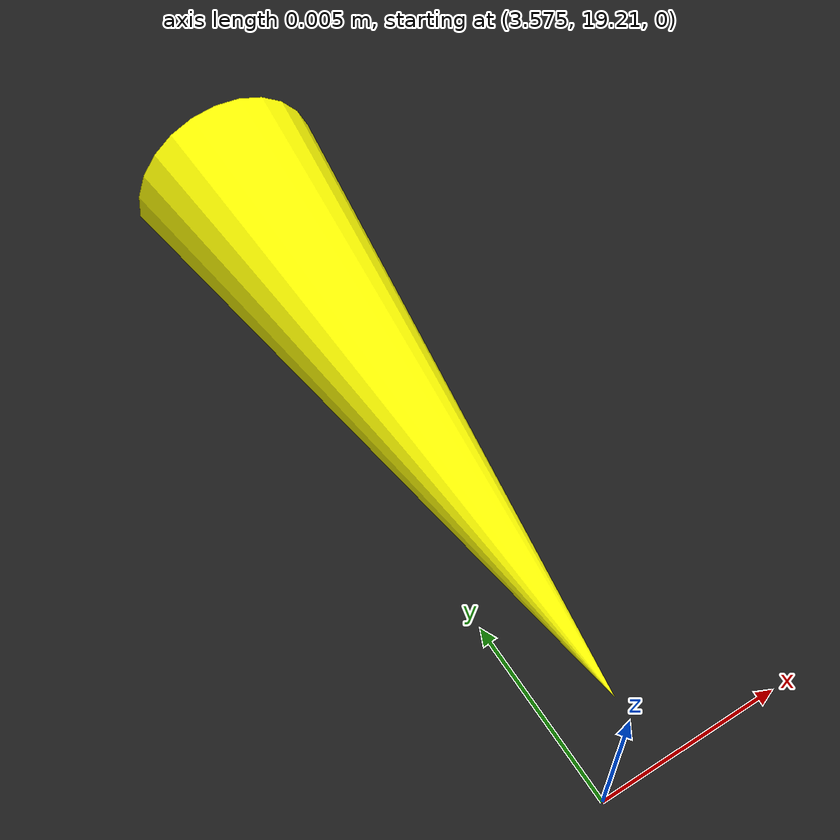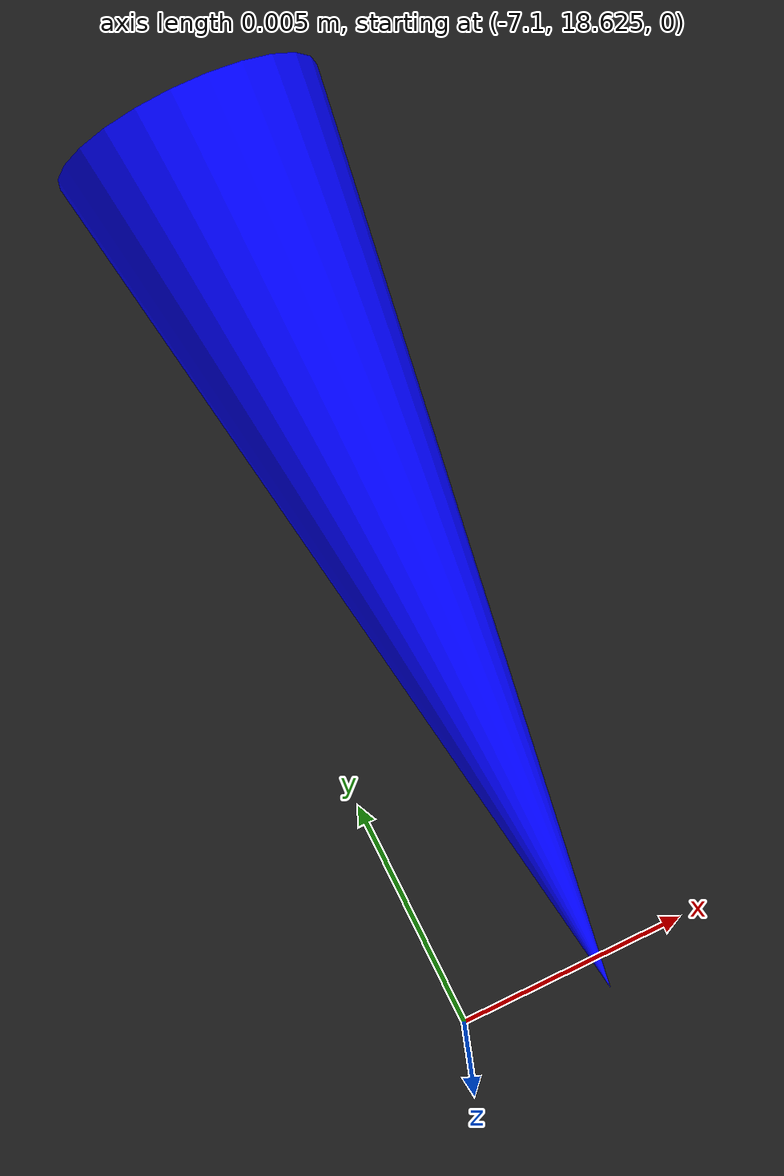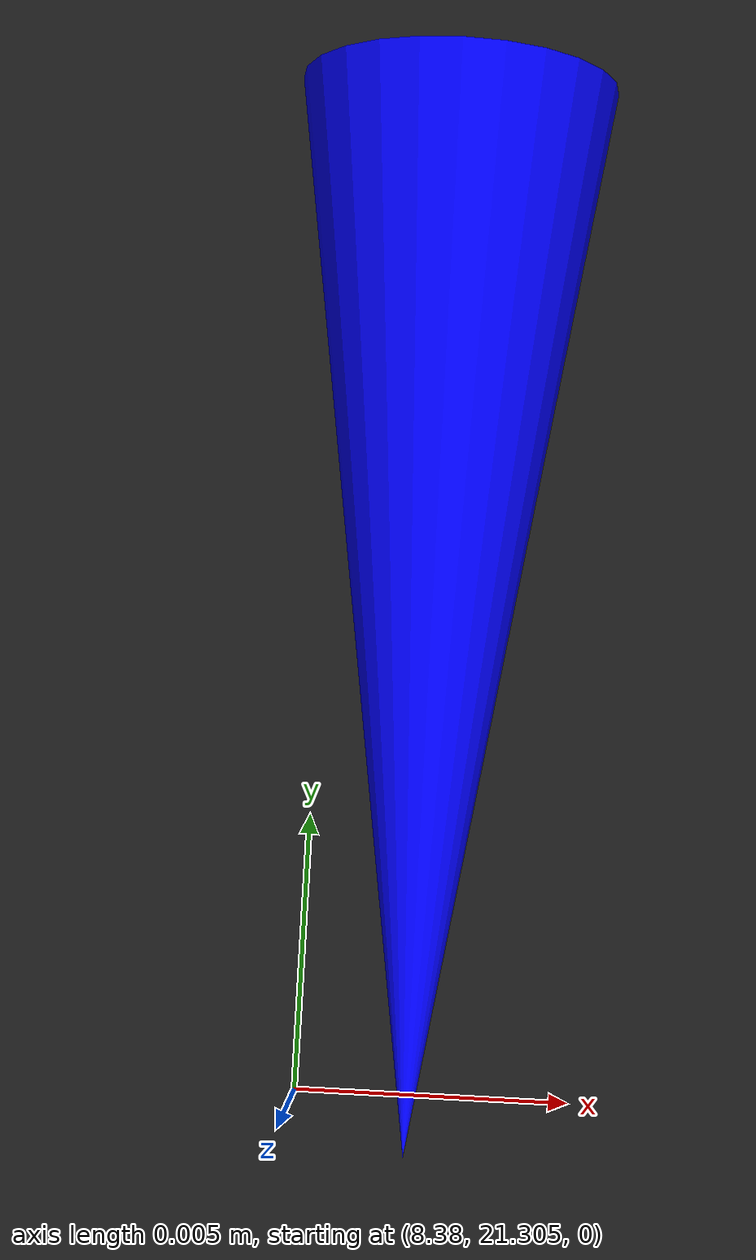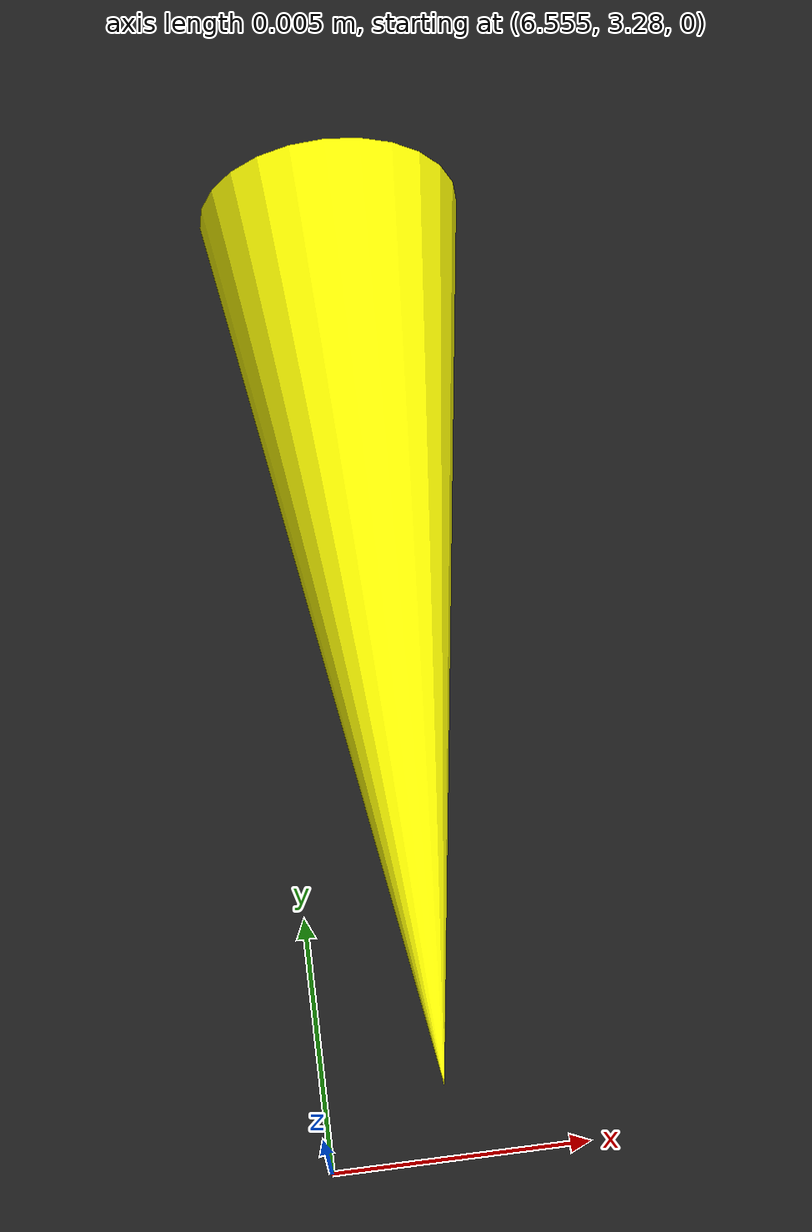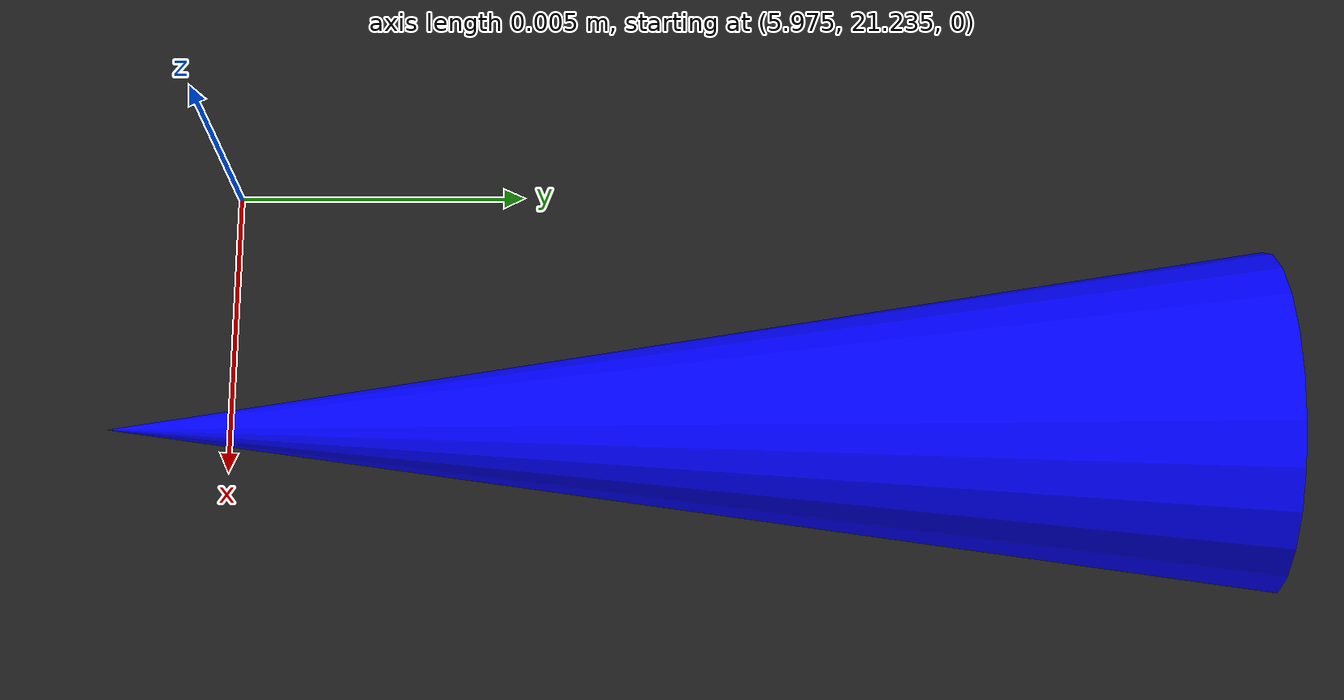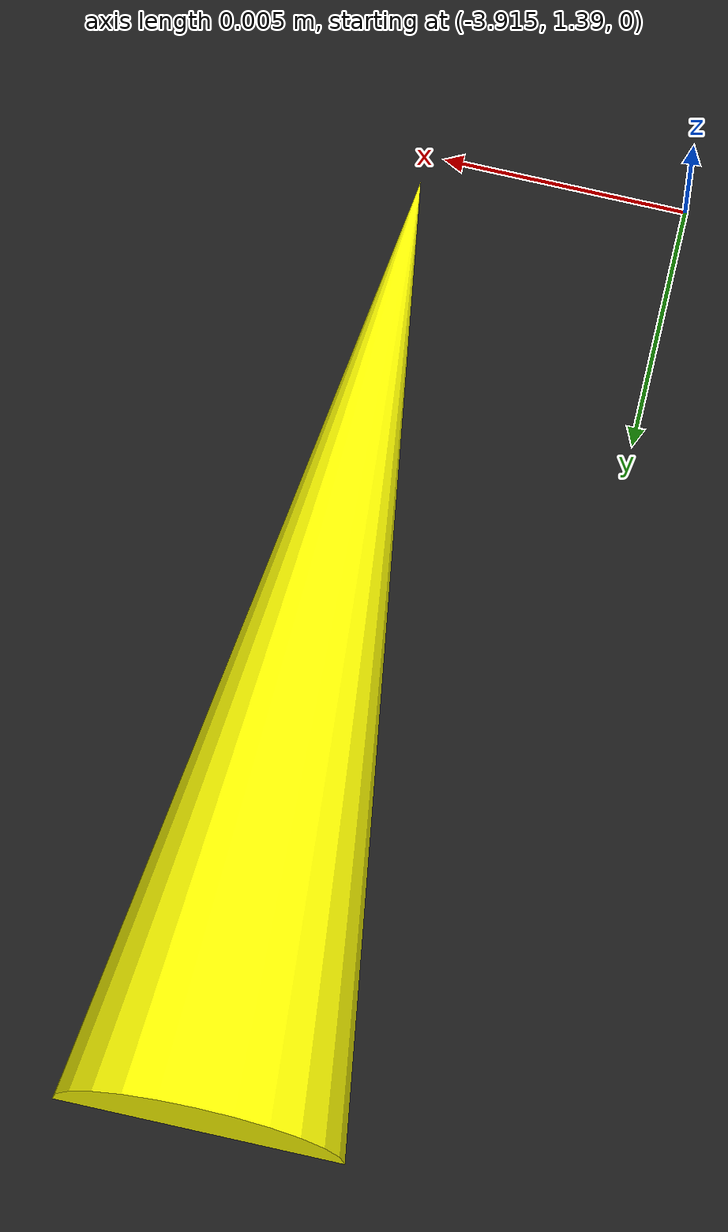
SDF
<?xml version="1.0"?>
  <sdf version='1.9'>
   <world name='track'>

        <!-- PHYSICS -->
        <physics name="1ms" type="ignored">
            <max_step_size>0.001</max_step_size>
            <real_time_factor>1.0</real_time_factor>
        </physics>

        <gravity>0 0 -9.8</gravity>
        <magnetic_field>6e-06 2.3e-05 -4.2e-05</magnetic_field>
        <atmosphere type='adiabatic'/>

        <!-- PLUGINS -->
        <plugin name='gz::sim::systems::Physics' filename='gz-sim-physics-system'/>
        <plugin name='gz::sim::systems::UserCommands' filename='gz-sim-user-commands-system'/>
        <plugin name='gz::sim::systems::SceneBroadcaster' filename='gz-sim-scene-broadcaster-system'/>

        <gui fullscreen='0'>
            <!-- 3D scene -->
            <plugin filename="MinimalScene" name="3D View">
                <gz-gui>
                <title>3D View</title>
                <property type="bool" key="showTitleBar">false</property>
                <property type="string" key="state">docked</property>
                </gz-gui>

                <engine>ogre2</engine>
                <scene>scene</scene>
                <ambient_light>0.4 0.4 0.4</ambient_light>
                <background_color>0.8 0.8 0.8</background_color>
                <camera_pose>-6 0 6 0 0.5 0</camera_pose>
            </plugin>

            <!-- Plugins that add functionality to the scene -->
            <plugin filename="EntityContextMenuPlugin" name="Entity context menu">
                <gz-gui>
                <property key="state" type="string">floating</property>
                <property key="width" type="double">5</property>
                <property key="height" type="double">5</property>
                <property key="showTitleBar" type="bool">false</property>
                </gz-gui>
            </plugin>
            <plugin filename="GzSceneManager" name="Scene Manager">
                <gz-gui>
                <property key="resizable" type="bool">false</property>
                <property key="width" type="double">5</property>
                <property key="height" type="double">5</property>
                <property key="state" type="string">floating</property>
                <property key="showTitleBar" type="bool">false</property>
                </gz-gui>
            </plugin>
            <plugin filename="InteractiveViewControl" name="Interactive view control">
                <gz-gui>
                <property key="resizable" type="bool">false</property>
                <property key="width" type="double">5</property>
                <property key="height" type="double">5</property>
                <property key="state" type="string">floating</property>
                <property key="showTitleBar" type="bool">false</property>
                </gz-gui>
            </plugin>
            <plugin filename="CameraTracking" name="Camera Tracking">
                <gz-gui>
                <property key="resizable" type="bool">false</property>
                <property key="width" type="double">5</property>
                <property key="height" type="double">5</property>
                <property key="state" type="string">floating</property>
                <property key="showTitleBar" type="bool">false</property>
                </gz-gui>
            </plugin>
            <plugin name='World control' filename='WorldControl'>
                <gz-gui>
                    <title>World control</title>
                    <property type='bool' key='showTitleBar'>0</property>
                    <property type='bool' key='resizable'>0</property>
                    <property type='double' key='height'>72</property>
                    <property type='double' key='z'>1</property>
                    <property type='string' key='state'>floating</property>
                    <anchors target='3D View'>
                        <line own='left' target='left'/>
                        <line own='bottom' target='bottom'/>
                    </anchors>
                </gz-gui>
                <play_pause>1</play_pause>
                <step>1</step>
                <start_paused>1</start_paused>
            </plugin>
            <plugin name='World stats' filename='WorldStats'>
                <gz-gui>
                    <title>World stats</title>
                    <property type='bool' key='showTitleBar'>0</property>
                    <property type='bool' key='resizable'>0</property>
                    <property type='double' key='height'>110</property>
                    <property type='double' key='width'>290</property>
                    <property type='double' key='z'>1</property>
                    <property type='string' key='state'>floating</property>
                    <anchors target='3D View'>
                        <line own='right' target='right'/>
                        <line own='bottom' target='bottom'/>
                    </anchors>
                </gz-gui>
                <sim_time>1</sim_time>
                <real_time>1</real_time>
                <real_time_factor>1</real_time_factor>
                <iterations>1</iterations>
            </plugin>

            <plugin filename="VisualizeLidar" name="Visualize Lidar">
            </plugin>

            <plugin filename="ImageDisplay" name="Image Display">
            </plugin>

            <!-- Inspector -->
            <plugin filename="ComponentInspector" name="Component inspector">
                <ignition-gui>
                <property type="string" key="state">docked</property>
                </ignition-gui>
            </plugin>

            <!-- Entity tree -->
            <plugin filename="EntityTree" name="Entity tree">
                <ignition-gui>
                <property type="string" key="state">docked</property>
                </ignition-gui>
            </plugin>
        </gui>

        <!-- SENSORS -->

        <plugin
        filename="gz-sim-sensors-system"
        name="gz::sim::systems::Sensors">
        <render_engine>ogre2</render_engine>
        </plugin>

        <!-- AMBIENT -->

        <scene>
            <ambient>1 1 1 1</ambient>
            <background>0.8 0.8 0.8 1</background>
            <shadows>1</shadows>
        </scene>
        <light name='sun' type='directional'>
            <cast_shadows>1</cast_shadows>
            <pose>0 0 10 0 0 0</pose>
            <diffuse>0.8 0.8 0.8 1</diffuse>
            <specular>0.8 0.8 0.8 1</specular>
            <attenuation>
                <range>1000</range>
                <constant>0.9</constant>
                <linear>0.01</linear>
                <quadratic>0.001</quadratic>
            </attenuation>
            <direction>-0.5 0.1 -0.9</direction>
        </light>

        <model name='ground_plane'>
            <static>true</static>
            <link name='link'>
                <collision name='collision'>
                    <geometry>
                        <plane>
                        <normal>0 0 1</normal>
                        <size>100 100</size>
                        </plane>
                    </geometry>

                    <surface>
                        <friction>
                            <dart/>
                        </friction>
                        <bounce/>
                        <contact/>
                    </surface>
                </collision>

                <visual name='visual'>
                    <geometry>
                        <plane>
                        <normal>0 0 1</normal>
                        <size>100 100</size>
                        </plane>
                    </geometry>
                    <material>
                        <ambient>0.1 0.1 0.1 1</ambient>
                        <diffuse>0.1 0.1 0.1 1</diffuse>
                        <specular>0.8 0.8 0.8 1</specular>
                    </material>
                </visual>

                <pose>0 0 0 0 -0 0</pose>

                <inertial>
                    <pose>0 0 0 0 -0 0</pose>
                    <mass>1</mass>
                    <inertia>
                        <ixx>1</ixx>
                        <ixy>0</ixy>
                        <ixz>0</ixz>
                        <iyy>1</iyy>
                        <iyz>0</iyz>
                        <izz>1</izz>
                    </inertia>
                </inertial>

                <enable_wind>false</enable_wind>

            </link>

            <pose>0 0 0 0 -0 0</pose>

            <self_collide>false</self_collide>
        </model>
     <model name='cone_0'>
      <link name='cone_0_link'>
        <inertial>
			<mass>0</mass>
			<inertia>
			<ixx>0.166667</ixx>
			<ixy>0</ixy>
			<ixz>0</ixz>
			<iyy>0.166667</iyy>
			<iyz>0</iyz>
			<izz>0.166667</izz>
			</inertia>
		</inertial>
        <collision name='cone_0_collision'>
          <geometry>
            <mesh>
              <uri>/models/cone/meshes/cone.stl</uri>
              <scale>0.001 0.001 0.001</scale>
            </mesh>
          </geometry>
        </collision>
        <visual name='cone_0_visual'>
          <geometry>
            <mesh>
              <uri>/models/cone/meshes/cone.stl</uri>
              <scale>0.001 0.001 0.001</scale>
            </mesh>
          </geometry>
          <material>
            <ambient>1 1 0 1</ambient>
            <diffuse>1 1 0 1</diffuse>
            <specular>1 1 0 1</specular>
          </material>
        </visual>

        <enable_wind>false</enable_wind>
      </link>
      <pose>5.382421556305033 19.280545577814365 0.0 1.57 0 0</pose>
      <static>true</static>
      </model>

     <model name='cone_1'>
      <link name='cone_1_link'>
        <inertial>
			<mass>0</mass>
			<inertia>
			<ixx>0.166667</ixx>
			<ixy>0</ixy>
			<ixz>0</ixz>
			<iyy>0.166667</iyy>
			<iyz>0</iyz>
			<izz>0.166667</izz>
			</inertia>
		</inertial>
        <collision name='cone_1_collision'>
          <geometry>
            <mesh>
              <uri>/models/cone/meshes/cone.stl</uri>
              <scale>0.001 0.001 0.001</scale>
            </mesh>
          </geometry>
        </collision>
        <visual name='cone_1_visual'>
          <geometry>
            <mesh>
              <uri>/models/cone/meshes/cone.stl</uri>
              <scale>0.001 0.001 0.001</scale>
            </mesh>
          </geometry>
          <material>
            <ambient>1 1 0 1</ambient>
            <diffuse>1 1 0 1</diffuse>
            <specular>1 1 0 1</specular>
          </material>
        </visual>

        <enable_wind>false</enable_wind>
      </link>
      <pose>6.579542595980271 19.319589401545894 0.0 1.57 0 0</pose>
      <static>true</static>
      </model>

     <model name='cone_2'>
      <link name='cone_2_link'>
        <inertial>
			<mass>0</mass>
			<inertia>
			<ixx>0.166667</ixx>
			<ixy>0</ixy>
			<ixz>0</ixz>
			<iyy>0.166667</iyy>
			<iyz>0</iyz>
			<izz>0.166667</izz>
			</inertia>
		</inertial>
        <collision name='cone_2_collision'>
          <geometry>
            <mesh>
              <uri>/models/cone/meshes/cone.stl</uri>
              <scale>0.001 0.001 0.001</scale>
            </mesh>
          </geometry>
        </collision>
        <visual name='cone_2_visual'>
          <geometry>
            <mesh>
              <uri>/models/cone/meshes/cone.stl</uri>
              <scale>0.001 0.001 0.001</scale>
            </mesh>
          </geometry>
          <material>
            <ambient>1 1 0 1</ambient>
            <diffuse>1 1 0 1</diffuse>
            <specular>1 1 0 1</specular>
          </material>
        </visual>

        <enable_wind>false</enable_wind>
      </link>
      <pose>7.771450202335582 19.355695193495464 0.0 1.57 0 0</pose>
      <static>true</static>
      </model>

     <model name='cone_3'>
      <link name='cone_3_link'>
        <inertial>
			<mass>0</mass>
			<inertia>
			<ixx>0.166667</ixx>
			<ixy>0</ixy>
			<ixz>0</ixz>
			<iyy>0.166667</iyy>
			<iyz>0</iyz>
			<izz>0.166667</izz>
			</inertia>
		</inertial>
        <collision name='cone_3_collision'>
          <geometry>
            <mesh>
              <uri>/models/cone/meshes/cone.stl</uri>
              <scale>0.001 0.001 0.001</scale>
            </mesh>
          </geometry>
        </collision>
        <visual name='cone_3_visual'>
          <geometry>
            <mesh>
              <uri>/models/cone/meshes/cone.stl</uri>
              <scale>0.001 0.001 0.001</scale>
            </mesh>
          </geometry>
          <material>
            <ambient>1 1 0 1</ambient>
            <diffuse>1 1 0 1</diffuse>
            <specular>1 1 0 1</specular>
          </material>
        </visual>

        <enable_wind>false</enable_wind>
      </link>
      <pose>10.140108875866432 19.391315532153424 0.0 1.57 0 0</pose>
      <static>true</static>
      </model>

     <model name='cone_4'>
      <link name='cone_4_link'>
        <inertial>
			<mass>0</mass>
			<inertia>
			<ixx>0.166667</ixx>
			<ixy>0</ixy>
			<ixz>0</ixz>
			<iyy>0.166667</iyy>
			<iyz>0</iyz>
			<izz>0.166667</izz>
			</inertia>
		</inertial>
        <collision name='cone_4_collision'>
          <geometry>
            <mesh>
              <uri>/models/cone/meshes/cone.stl</uri>
              <scale>0.001 0.001 0.001</scale>
            </mesh>
          </geometry>
        </collision>
        <visual name='cone_4_visual'>
          <geometry>
            <mesh>
              <uri>/models/cone/meshes/cone.stl</uri>
              <scale>0.001 0.001 0.001</scale>
            </mesh>
          </geometry>
          <material>
            <ambient>1 1 0 1</ambient>
            <diffuse>1 1 0 1</diffuse>
            <specular>1 1 0 1</specular>
          </material>
        </visual>

        <enable_wind>false</enable_wind>
      </link>
      <pose>11.31654817571297 19.377171033627306 0.0 1.57 0 0</pose>
      <static>true</static>
      </model>

     <model name='cone_5'>
      <link name='cone_5_link'>
        <inertial>
			<mass>0</mass>
			<inertia>
			<ixx>0.166667</ixx>
			<ixy>0</ixy>
			<ixz>0</ixz>
			<iyy>0.166667</iyy>
			<iyz>0</iyz>
			<izz>0.166667</izz>
			</inertia>
		</inertial>
        <collision name='cone_5_collision'>
          <geometry>
            <mesh>
              <uri>/models/cone/meshes/cone.stl</uri>
              <scale>0.001 0.001 0.001</scale>
            </mesh>
          </geometry>
        </collision>
        <visual name='cone_5_visual'>
          <geometry>
            <mesh>
              <uri>/models/cone/meshes/cone.stl</uri>
              <scale>0.001 0.001 0.001</scale>
            </mesh>
          </geometry>
          <material>
            <ambient>1 1 0 1</ambient>
            <diffuse>1 1 0 1</diffuse>
            <specular>1 1 0 1</specular>
          </material>
        </visual>

        <enable_wind>false</enable_wind>
      </link>
      <pose>12.486914520177981 19.332785438770387 0.0 1.57 0 0</pose>
      <static>true</static>
      </model>

     <model name='cone_6'>
      <link name='cone_6_link'>
        <inertial>
			<mass>0</mass>
			<inertia>
			<ixx>0.166667</ixx>
			<ixy>0</ixy>
			<ixz>0</ixz>
			<iyy>0.166667</iyy>
			<iyz>0</iyz>
			<izz>0.166667</izz>
			</inertia>
		</inertial>
        <collision name='cone_6_collision'>
          <geometry>
            <mesh>
              <uri>/models/cone/meshes/cone.stl</uri>
              <scale>0.001 0.001 0.001</scale>
            </mesh>
          </geometry>
        </collision>
        <visual name='cone_6_visual'>
          <geometry>
            <mesh>
              <uri>/models/cone/meshes/cone.stl</uri>
              <scale>0.001 0.001 0.001</scale>
            </mesh>
          </geometry>
          <material>
            <ambient>1 1 0 1</ambient>
            <diffuse>1 1 0 1</diffuse>
            <specular>1 1 0 1</specular>
          </material>
        </visual>

        <enable_wind>false</enable_wind>
      </link>
      <pose>13.598596021164262 19.236297320702313 0.0 1.57 0 0</pose>
      <static>true</static>
      </model>

     <model name='cone_7'>
      <link name='cone_7_link'>
        <inertial>
			<mass>0</mass>
			<inertia>
			<ixx>0.166667</ixx>
			<ixy>0</ixy>
			<ixz>0</ixz>
			<iyy>0.166667</iyy>
			<iyz>0</iyz>
			<izz>0.166667</izz>
			</inertia>
		</inertial>
        <collision name='cone_7_collision'>
          <geometry>
            <mesh>
              <uri>/models/cone/meshes/cone.stl</uri>
              <scale>0.001 0.001 0.001</scale>
            </mesh>
          </geometry>
        </collision>
        <visual name='cone_7_visual'>
          <geometry>
            <mesh>
              <uri>/models/cone/meshes/cone.stl</uri>
              <scale>0.001 0.001 0.001</scale>
            </mesh>
          </geometry>
          <material>
            <ambient>1 1 0 1</ambient>
            <diffuse>1 1 0 1</diffuse>
            <specular>1 1 0 1</specular>
          </material>
        </visual>

        <enable_wind>false</enable_wind>
      </link>
      <pose>14.98732005122477 18.807827215176992 0.0 1.57 0 0</pose>
      <static>true</static>
      </model>

     <model name='cone_8'>
      <link name='cone_8_link'>
        <inertial>
			<mass>0</mass>
			<inertia>
			<ixx>0.166667</ixx>
			<ixy>0</ixy>
			<ixz>0</ixz>
			<iyy>0.166667</iyy>
			<iyz>0</iyz>
			<izz>0.166667</izz>
			</inertia>
		</inertial>
        <collision name='cone_8_collision'>
          <geometry>
            <mesh>
              <uri>/models/cone/meshes/cone.stl</uri>
              <scale>0.001 0.001 0.001</scale>
            </mesh>
          </geometry>
        </collision>
        <visual name='cone_8_visual'>
          <geometry>
            <mesh>
              <uri>/models/cone/meshes/cone.stl</uri>
              <scale>0.001 0.001 0.001</scale>
            </mesh>
          </geometry>
          <material>
            <ambient>1 1 0 1</ambient>
            <diffuse>1 1 0 1</diffuse>
            <specular>1 1 0 1</specular>
          </material>
        </visual>

        <enable_wind>false</enable_wind>
      </link>
      <pose>15.926920423094751 17.876054415822754 0.0 1.57 0 0</pose>
      <static>true</static>
      </model>

     <model name='cone_9'>
      <link name='cone_9_link'>
        <inertial>
			<mass>0</mass>
			<inertia>
			<ixx>0.166667</ixx>
			<ixy>0</ixy>
			<ixz>0</ixz>
			<iyy>0.166667</iyy>
			<iyz>0</iyz>
			<izz>0.166667</izz>
			</inertia>
		</inertial>
        <collision name='cone_9_collision'>
          <geometry>
            <mesh>
              <uri>/models/cone/meshes/cone.stl</uri>
              <scale>0.001 0.001 0.001</scale>
            </mesh>
          </geometry>
        </collision>
        <visual name='cone_9_visual'>
          <geometry>
            <mesh>
              <uri>/models/cone/meshes/cone.stl</uri>
              <scale>0.001 0.001 0.001</scale>
            </mesh>
          </geometry>
          <material>
            <ambient>1 1 0 1</ambient>
            <diffuse>1 1 0 1</diffuse>
            <specular>1 1 0 1</specular>
          </material>
        </visual>

        <enable_wind>false</enable_wind>
      </link>
      <pose>16.31120242529576 16.995498056990435 0.0 1.57 0 0</pose>
      <static>true</static>
      </model>

     <model name='cone_10'>
      <link name='cone_10_link'>
        <inertial>
			<mass>0</mass>
			<inertia>
			<ixx>0.166667</ixx>
			<ixy>0</ixy>
			<ixz>0</ixz>
			<iyy>0.166667</iyy>
			<iyz>0</iyz>
			<izz>0.166667</izz>
			</inertia>
		</inertial>
        <collision name='cone_10_collision'>
          <geometry>
            <mesh>
              <uri>/models/cone/meshes/cone.stl</uri>
              <scale>0.001 0.001 0.001</scale>
            </mesh>
          </geometry>
        </collision>
        <visual name='cone_10_visual'>
          <geometry>
            <mesh>
              <uri>/models/cone/meshes/cone.stl</uri>
              <scale>0.001 0.001 0.001</scale>
            </mesh>
          </geometry>
          <material>
            <ambient>1 1 0 1</ambient>
            <diffuse>1 1 0 1</diffuse>
            <specular>1 1 0 1</specular>
          </material>
        </visual>

        <enable_wind>false</enable_wind>
      </link>
      <pose>16.45533481062494 15.569344923634326 0.0 1.57 0 0</pose>
      <static>true</static>
      </model>

     <model name='cone_11'>
      <link name='cone_11_link'>
        <inertial>
			<mass>0</mass>
			<inertia>
			<ixx>0.166667</ixx>
			<ixy>0</ixy>
			<ixz>0</ixz>
			<iyy>0.166667</iyy>
			<iyz>0</iyz>
			<izz>0.166667</izz>
			</inertia>
		</inertial>
        <collision name='cone_11_collision'>
          <geometry>
            <mesh>
              <uri>/models/cone/meshes/cone.stl</uri>
              <scale>0.001 0.001 0.001</scale>
            </mesh>
          </geometry>
        </collision>
        <visual name='cone_11_visual'>
          <geometry>
            <mesh>
              <uri>/models/cone/meshes/cone.stl</uri>
              <scale>0.001 0.001 0.001</scale>
            </mesh>
          </geometry>
          <material>
            <ambient>1 1 0 1</ambient>
            <diffuse>1 1 0 1</diffuse>
            <specular>1 1 0 1</specular>
          </material>
        </visual>

        <enable_wind>false</enable_wind>
      </link>
      <pose>16.225281470202233 14.681312221823195 0.0 1.57 0 0</pose>
      <static>true</static>
      </model>

     <model name='cone_12'>
      <link name='cone_12_link'>
        <inertial>
			<mass>0</mass>
			<inertia>
			<ixx>0.166667</ixx>
			<ixy>0</ixy>
			<ixz>0</ixz>
			<iyy>0.166667</iyy>
			<iyz>0</iyz>
			<izz>0.166667</izz>
			</inertia>
		</inertial>
        <collision name='cone_12_collision'>
          <geometry>
            <mesh>
              <uri>/models/cone/meshes/cone.stl</uri>
              <scale>0.001 0.001 0.001</scale>
            </mesh>
          </geometry>
        </collision>
        <visual name='cone_12_visual'>
          <geometry>
            <mesh>
              <uri>/models/cone/meshes/cone.stl</uri>
              <scale>0.001 0.001 0.001</scale>
            </mesh>
          </geometry>
          <material>
            <ambient>1 1 0 1</ambient>
            <diffuse>1 1 0 1</diffuse>
            <specular>1 1 0 1</specular>
          </material>
        </visual>

        <enable_wind>false</enable_wind>
      </link>
      <pose>15.388881715216941 13.560876533857083 0.0 1.57 0 0</pose>
      <static>true</static>
      </model>

     <model name='cone_13'>
      <link name='cone_13_link'>
        <inertial>
			<mass>0</mass>
			<inertia>
			<ixx>0.166667</ixx>
			<ixy>0</ixy>
			<ixz>0</ixz>
			<iyy>0.166667</iyy>
			<iyz>0</iyz>
			<izz>0.166667</izz>
			</inertia>
		</inertial>
        <collision name='cone_13_collision'>
          <geometry>
            <mesh>
              <uri>/models/cone/meshes/cone.stl</uri>
              <scale>0.001 0.001 0.001</scale>
            </mesh>
          </geometry>
        </collision>
        <visual name='cone_13_visual'>
          <geometry>
            <mesh>
              <uri>/models/cone/meshes/cone.stl</uri>
              <scale>0.001 0.001 0.001</scale>
            </mesh>
          </geometry>
          <material>
            <ambient>1 1 0 1</ambient>
            <diffuse>1 1 0 1</diffuse>
            <specular>1 1 0 1</specular>
          </material>
        </visual>

        <enable_wind>false</enable_wind>
      </link>
      <pose>14.127242563316573 12.757298860133885 0.0 1.57 0 0</pose>
      <static>true</static>
      </model>

     <model name='cone_14'>
      <link name='cone_14_link'>
        <inertial>
			<mass>0</mass>
			<inertia>
			<ixx>0.166667</ixx>
			<ixy>0</ixy>
			<ixz>0</ixz>
			<iyy>0.166667</iyy>
			<iyz>0</iyz>
			<izz>0.166667</izz>
			</inertia>
		</inertial>
        <collision name='cone_14_collision'>
          <geometry>
            <mesh>
              <uri>/models/cone/meshes/cone.stl</uri>
              <scale>0.001 0.001 0.001</scale>
            </mesh>
          </geometry>
        </collision>
        <visual name='cone_14_visual'>
          <geometry>
            <mesh>
              <uri>/models/cone/meshes/cone.stl</uri>
              <scale>0.001 0.001 0.001</scale>
            </mesh>
          </geometry>
          <material>
            <ambient>1 1 0 1</ambient>
            <diffuse>1 1 0 1</diffuse>
            <specular>1 1 0 1</specular>
          </material>
        </visual>

        <enable_wind>false</enable_wind>
      </link>
      <pose>13.18759043215979 12.480163092645665 0.0 1.57 0 0</pose>
      <static>true</static>
      </model>

     <model name='cone_15'>
      <link name='cone_15_link'>
        <inertial>
			<mass>0</mass>
			<inertia>
			<ixx>0.166667</ixx>
			<ixy>0</ixy>
			<ixz>0</ixz>
			<iyy>0.166667</iyy>
			<iyz>0</iyz>
			<izz>0.166667</izz>
			</inertia>
		</inertial>
        <collision name='cone_15_collision'>
          <geometry>
            <mesh>
              <uri>/models/cone/meshes/cone.stl</uri>
              <scale>0.001 0.001 0.001</scale>
            </mesh>
          </geometry>
        </collision>
        <visual name='cone_15_visual'>
          <geometry>
            <mesh>
              <uri>/models/cone/meshes/cone.stl</uri>
              <scale>0.001 0.001 0.001</scale>
            </mesh>
          </geometry>
          <material>
            <ambient>1 1 0 1</ambient>
            <diffuse>1 1 0 1</diffuse>
            <specular>1 1 0 1</specular>
          </material>
        </visual>

        <enable_wind>false</enable_wind>
      </link>
      <pose>12.225585970688662 12.445242920354584 0.0 1.57 0 0</pose>
      <static>true</static>
      </model>

     <model name='cone_16'>
      <link name='cone_16_link'>
        <inertial>
			<mass>0</mass>
			<inertia>
			<ixx>0.166667</ixx>
			<ixy>0</ixy>
			<ixz>0</ixz>
			<iyy>0.166667</iyy>
			<iyz>0</iyz>
			<izz>0.166667</izz>
			</inertia>
		</inertial>
        <collision name='cone_16_collision'>
          <geometry>
            <mesh>
              <uri>/models/cone/meshes/cone.stl</uri>
              <scale>0.001 0.001 0.001</scale>
            </mesh>
          </geometry>
        </collision>
        <visual name='cone_16_visual'>
          <geometry>
            <mesh>
              <uri>/models/cone/meshes/cone.stl</uri>
              <scale>0.001 0.001 0.001</scale>
            </mesh>
          </geometry>
          <material>
            <ambient>1 1 0 1</ambient>
            <diffuse>1 1 0 1</diffuse>
            <specular>1 1 0 1</specular>
          </material>
        </visual>

        <enable_wind>false</enable_wind>
      </link>
      <pose>10.776853441702702 12.835995826100584 0.0 1.57 0 0</pose>
      <static>true</static>
      </model>

     <model name='cone_17'>
      <link name='cone_17_link'>
        <inertial>
			<mass>0</mass>
			<inertia>
			<ixx>0.166667</ixx>
			<ixy>0</ixy>
			<ixz>0</ixz>
			<iyy>0.166667</iyy>
			<iyz>0</iyz>
			<izz>0.166667</izz>
			</inertia>
		</inertial>
        <collision name='cone_17_collision'>
          <geometry>
            <mesh>
              <uri>/models/cone/meshes/cone.stl</uri>
              <scale>0.001 0.001 0.001</scale>
            </mesh>
          </geometry>
        </collision>
        <visual name='cone_17_visual'>
          <geometry>
            <mesh>
              <uri>/models/cone/meshes/cone.stl</uri>
              <scale>0.001 0.001 0.001</scale>
            </mesh>
          </geometry>
          <material>
            <ambient>1 1 0 1</ambient>
            <diffuse>1 1 0 1</diffuse>
            <specular>1 1 0 1</specular>
          </material>
        </visual>

        <enable_wind>false</enable_wind>
      </link>
      <pose>9.37624566488375 13.652127665448663 0.0 1.57 0 0</pose>
      <static>true</static>
      </model>

     <model name='cone_18'>
      <link name='cone_18_link'>
        <inertial>
			<mass>0</mass>
			<inertia>
			<ixx>0.166667</ixx>
			<ixy>0</ixy>
			<ixz>0</ixz>
			<iyy>0.166667</iyy>
			<iyz>0</iyz>
			<izz>0.166667</izz>
			</inertia>
		</inertial>
        <collision name='cone_18_collision'>
          <geometry>
            <mesh>
              <uri>/models/cone/meshes/cone.stl</uri>
              <scale>0.001 0.001 0.001</scale>
            </mesh>
          </geometry>
        </collision>
        <visual name='cone_18_visual'>
          <geometry>
            <mesh>
              <uri>/models/cone/meshes/cone.stl</uri>
              <scale>0.001 0.001 0.001</scale>
            </mesh>
          </geometry>
          <material>
            <ambient>1 1 0 1</ambient>
            <diffuse>1 1 0 1</diffuse>
            <specular>1 1 0 1</specular>
          </material>
        </visual>

        <enable_wind>false</enable_wind>
      </link>
      <pose>8.39283469653203 14.342214265248753 0.0 1.57 0 0</pose>
      <static>true</static>
      </model>

     <model name='cone_19'>
      <link name='cone_19_link'>
        <inertial>
			<mass>0</mass>
			<inertia>
			<ixx>0.166667</ixx>
			<ixy>0</ixy>
			<ixz>0</ixz>
			<iyy>0.166667</iyy>
			<iyz>0</iyz>
			<izz>0.166667</izz>
			</inertia>
		</inertial>
        <collision name='cone_19_collision'>
          <geometry>
            <mesh>
              <uri>/models/cone/meshes/cone.stl</uri>
              <scale>0.001 0.001 0.001</scale>
            </mesh>
          </geometry>
        </collision>
        <visual name='cone_19_visual'>
          <geometry>
            <mesh>
              <uri>/models/cone/meshes/cone.stl</uri>
              <scale>0.001 0.001 0.001</scale>
            </mesh>
          </geometry>
          <material>
            <ambient>1 1 0 1</ambient>
            <diffuse>1 1 0 1</diffuse>
            <specular>1 1 0 1</specular>
          </material>
        </visual>

        <enable_wind>false</enable_wind>
      </link>
      <pose>6.6610650286904916 15.312559773794284 0.0 1.57 0 0</pose>
      <static>true</static>
      </model>

     <model name='cone_20'>
      <link name='cone_20_link'>
        <inertial>
			<mass>0</mass>
			<inertia>
			<ixx>0.166667</ixx>
			<ixy>0</ixy>
			<ixz>0</ixz>
			<iyy>0.166667</iyy>
			<iyz>0</iyz>
			<izz>0.166667</izz>
			</inertia>
		</inertial>
        <collision name='cone_20_collision'>
          <geometry>
            <mesh>
              <uri>/models/cone/meshes/cone.stl</uri>
              <scale>0.001 0.001 0.001</scale>
            </mesh>
          </geometry>
        </collision>
        <visual name='cone_20_visual'>
          <geometry>
            <mesh>
              <uri>/models/cone/meshes/cone.stl</uri>
              <scale>0.001 0.001 0.001</scale>
            </mesh>
          </geometry>
          <material>
            <ambient>1 1 0 1</ambient>
            <diffuse>1 1 0 1</diffuse>
            <specular>1 1 0 1</specular>
          </material>
        </visual>

        <enable_wind>false</enable_wind>
      </link>
      <pose>5.3449904799577865 15.699920195025875 0.0 1.57 0 0</pose>
      <static>true</static>
      </model>

     <model name='cone_21'>
      <link name='cone_21_link'>
        <inertial>
			<mass>0</mass>
			<inertia>
			<ixx>0.166667</ixx>
			<ixy>0</ixy>
			<ixz>0</ixz>
			<iyy>0.166667</iyy>
			<iyz>0</iyz>
			<izz>0.166667</izz>
			</inertia>
		</inertial>
        <collision name='cone_21_collision'>
          <geometry>
            <mesh>
              <uri>/models/cone/meshes/cone.stl</uri>
              <scale>0.001 0.001 0.001</scale>
            </mesh>
          </geometry>
        </collision>
        <visual name='cone_21_visual'>
          <geometry>
            <mesh>
              <uri>/models/cone/meshes/cone.stl</uri>
              <scale>0.001 0.001 0.001</scale>
            </mesh>
          </geometry>
          <material>
            <ambient>1 1 0 1</ambient>
            <diffuse>1 1 0 1</diffuse>
            <specular>1 1 0 1</specular>
          </material>
        </visual>

        <enable_wind>false</enable_wind>
      </link>
      <pose>3.312288118679591 15.803889548975373 0.0 1.57 0 0</pose>
      <static>true</static>
      </model>

     <model name='cone_22'>
      <link name='cone_22_link'>
        <inertial>
			<mass>0</mass>
			<inertia>
			<ixx>0.166667</ixx>
			<ixy>0</ixy>
			<ixz>0</ixz>
			<iyy>0.166667</iyy>
			<iyz>0</iyz>
			<izz>0.166667</izz>
			</inertia>
		</inertial>
        <collision name='cone_22_collision'>
          <geometry>
            <mesh>
              <uri>/models/cone/meshes/cone.stl</uri>
              <scale>0.001 0.001 0.001</scale>
            </mesh>
          </geometry>
        </collision>
        <visual name='cone_22_visual'>
          <geometry>
            <mesh>
              <uri>/models/cone/meshes/cone.stl</uri>
              <scale>0.001 0.001 0.001</scale>
            </mesh>
          </geometry>
          <material>
            <ambient>1 1 0 1</ambient>
            <diffuse>1 1 0 1</diffuse>
            <specular>1 1 0 1</specular>
          </material>
        </visual>

        <enable_wind>false</enable_wind>
      </link>
      <pose>1.1749817226177068 15.087775040986863 0.0 1.57 0 0</pose>
      <static>true</static>
      </model>

     <model name='cone_23'>
      <link name='cone_23_link'>
        <inertial>
			<mass>0</mass>
			<inertia>
			<ixx>0.166667</ixx>
			<ixy>0</ixy>
			<ixz>0</ixz>
			<iyy>0.166667</iyy>
			<iyz>0</iyz>
			<izz>0.166667</izz>
			</inertia>
		</inertial>
        <collision name='cone_23_collision'>
          <geometry>
            <mesh>
              <uri>/models/cone/meshes/cone.stl</uri>
              <scale>0.001 0.001 0.001</scale>
            </mesh>
          </geometry>
        </collision>
        <visual name='cone_23_visual'>
          <geometry>
            <mesh>
              <uri>/models/cone/meshes/cone.stl</uri>
              <scale>0.001 0.001 0.001</scale>
            </mesh>
          </geometry>
          <material>
            <ambient>1 1 0 1</ambient>
            <diffuse>1 1 0 1</diffuse>
            <specular>1 1 0 1</specular>
          </material>
        </visual>

        <enable_wind>false</enable_wind>
      </link>
      <pose>0.13505786586335145 13.792268334967503 0.0 1.57 0 0</pose>
      <static>true</static>
      </model>

     <model name='cone_24'>
      <link name='cone_24_link'>
        <inertial>
			<mass>0</mass>
			<inertia>
			<ixx>0.166667</ixx>
			<ixy>0</ixy>
			<ixz>0</ixz>
			<iyy>0.166667</iyy>
			<iyz>0</iyz>
			<izz>0.166667</izz>
			</inertia>
		</inertial>
        <collision name='cone_24_collision'>
          <geometry>
            <mesh>
              <uri>/models/cone/meshes/cone.stl</uri>
              <scale>0.001 0.001 0.001</scale>
            </mesh>
          </geometry>
        </collision>
        <visual name='cone_24_visual'>
          <geometry>
            <mesh>
              <uri>/models/cone/meshes/cone.stl</uri>
              <scale>0.001 0.001 0.001</scale>
            </mesh>
          </geometry>
          <material>
            <ambient>1 1 0 1</ambient>
            <diffuse>1 1 0 1</diffuse>
            <specular>1 1 0 1</specular>
          </material>
        </visual>

        <enable_wind>false</enable_wind>
      </link>
      <pose>-0.10428655304277701 12.161838474503403 0.0 1.57 0 0</pose>
      <static>true</static>
      </model>

     <model name='cone_25'>
      <link name='cone_25_link'>
        <inertial>
			<mass>0</mass>
			<inertia>
			<ixx>0.166667</ixx>
			<ixy>0</ixy>
			<ixz>0</ixz>
			<iyy>0.166667</iyy>
			<iyz>0</iyz>
			<izz>0.166667</izz>
			</inertia>
		</inertial>
        <collision name='cone_25_collision'>
          <geometry>
            <mesh>
              <uri>/models/cone/meshes/cone.stl</uri>
              <scale>0.001 0.001 0.001</scale>
            </mesh>
          </geometry>
        </collision>
        <visual name='cone_25_visual'>
          <geometry>
            <mesh>
              <uri>/models/cone/meshes/cone.stl</uri>
              <scale>0.001 0.001 0.001</scale>
            </mesh>
          </geometry>
          <material>
            <ambient>1 1 0 1</ambient>
            <diffuse>1 1 0 1</diffuse>
            <specular>1 1 0 1</specular>
          </material>
        </visual>

        <enable_wind>false</enable_wind>
      </link>
      <pose>0.48109059517234876 10.637689559846434 0.0 1.57 0 0</pose>
      <static>true</static>
      </model>

     <model name='cone_26'>
      <link name='cone_26_link'>
        <inertial>
			<mass>0</mass>
			<inertia>
			<ixx>0.166667</ixx>
			<ixy>0</ixy>
			<ixz>0</ixz>
			<iyy>0.166667</iyy>
			<iyz>0</iyz>
			<izz>0.166667</izz>
			</inertia>
		</inertial>
        <collision name='cone_26_collision'>
          <geometry>
            <mesh>
              <uri>/models/cone/meshes/cone.stl</uri>
              <scale>0.001 0.001 0.001</scale>
            </mesh>
          </geometry>
        </collision>
        <visual name='cone_26_visual'>
          <geometry>
            <mesh>
              <uri>/models/cone/meshes/cone.stl</uri>
              <scale>0.001 0.001 0.001</scale>
            </mesh>
          </geometry>
          <material>
            <ambient>1 1 0 1</ambient>
            <diffuse>1 1 0 1</diffuse>
            <specular>1 1 0 1</specular>
          </material>
        </visual>

        <enable_wind>false</enable_wind>
      </link>
      <pose>2.639614541134468 8.959926946439026 0.0 1.57 0 0</pose>
      <static>true</static>
      </model>

     <model name='cone_27'>
      <link name='cone_27_link'>
        <inertial>
			<mass>0</mass>
			<inertia>
			<ixx>0.166667</ixx>
			<ixy>0</ixy>
			<ixz>0</ixz>
			<iyy>0.166667</iyy>
			<iyz>0</iyz>
			<izz>0.166667</izz>
			</inertia>
		</inertial>
        <collision name='cone_27_collision'>
          <geometry>
            <mesh>
              <uri>/models/cone/meshes/cone.stl</uri>
              <scale>0.001 0.001 0.001</scale>
            </mesh>
          </geometry>
        </collision>
        <visual name='cone_27_visual'>
          <geometry>
            <mesh>
              <uri>/models/cone/meshes/cone.stl</uri>
              <scale>0.001 0.001 0.001</scale>
            </mesh>
          </geometry>
          <material>
            <ambient>1 1 0 1</ambient>
            <diffuse>1 1 0 1</diffuse>
            <specular>1 1 0 1</specular>
          </material>
        </visual>

        <enable_wind>false</enable_wind>
      </link>
      <pose>3.392332124037867 8.382803883774287 0.0 1.57 0 0</pose>
      <static>true</static>
      </model>

     <model name='cone_28'>
      <link name='cone_28_link'>
        <inertial>
			<mass>0</mass>
			<inertia>
			<ixx>0.166667</ixx>
			<ixy>0</ixy>
			<ixz>0</ixz>
			<iyy>0.166667</iyy>
			<iyz>0</iyz>
			<izz>0.166667</izz>
			</inertia>
		</inertial>
        <collision name='cone_28_collision'>
          <geometry>
            <mesh>
              <uri>/models/cone/meshes/cone.stl</uri>
              <scale>0.001 0.001 0.001</scale>
            </mesh>
          </geometry>
        </collision>
        <visual name='cone_28_visual'>
          <geometry>
            <mesh>
              <uri>/models/cone/meshes/cone.stl</uri>
              <scale>0.001 0.001 0.001</scale>
            </mesh>
          </geometry>
          <material>
            <ambient>1 1 0 1</ambient>
            <diffuse>1 1 0 1</diffuse>
            <specular>1 1 0 1</specular>
          </material>
        </visual>

        <enable_wind>false</enable_wind>
      </link>
      <pose>3.736620134251825 7.736872165010185 0.0 1.57 0 0</pose>
      <static>true</static>
      </model>

     <model name='cone_29'>
      <link name='cone_29_link'>
        <inertial>
			<mass>0</mass>
			<inertia>
			<ixx>0.166667</ixx>
			<ixy>0</ixy>
			<ixz>0</ixz>
			<iyy>0.166667</iyy>
			<iyz>0</iyz>
			<izz>0.166667</izz>
			</inertia>
		</inertial>
        <collision name='cone_29_collision'>
          <geometry>
            <mesh>
              <uri>/models/cone/meshes/cone.stl</uri>
              <scale>0.001 0.001 0.001</scale>
            </mesh>
          </geometry>
        </collision>
        <visual name='cone_29_visual'>
          <geometry>
            <mesh>
              <uri>/models/cone/meshes/cone.stl</uri>
              <scale>0.001 0.001 0.001</scale>
            </mesh>
          </geometry>
          <material>
            <ambient>1 1 0 1</ambient>
            <diffuse>1 1 0 1</diffuse>
            <specular>1 1 0 1</specular>
          </material>
        </visual>

        <enable_wind>false</enable_wind>
      </link>
      <pose>3.9463893396575016 6.0084003942289534 0.0 1.57 0 0</pose>
      <static>true</static>
      </model>

     <model name='cone_30'>
      <link name='cone_30_link'>
        <inertial>
			<mass>0</mass>
			<inertia>
			<ixx>0.166667</ixx>
			<ixy>0</ixy>
			<ixz>0</ixz>
			<iyy>0.166667</iyy>
			<iyz>0</iyz>
			<izz>0.166667</izz>
			</inertia>
		</inertial>
        <collision name='cone_30_collision'>
          <geometry>
            <mesh>
              <uri>/models/cone/meshes/cone.stl</uri>
              <scale>0.001 0.001 0.001</scale>
            </mesh>
          </geometry>
        </collision>
        <visual name='cone_30_visual'>
          <geometry>
            <mesh>
              <uri>/models/cone/meshes/cone.stl</uri>
              <scale>0.001 0.001 0.001</scale>
            </mesh>
          </geometry>
          <material>
            <ambient>1 1 0 1</ambient>
            <diffuse>1 1 0 1</diffuse>
            <specular>1 1 0 1</specular>
          </material>
        </visual>

        <enable_wind>false</enable_wind>
      </link>
      <pose>5.204436350466808 3.9501479700849966 0.0 1.57 0 0</pose>
      <static>true</static>
      </model>

     <model name='cone_31'>
      <link name='cone_31_link'>
        <inertial>
			<mass>0</mass>
			<inertia>
			<ixx>0.166667</ixx>
			<ixy>0</ixy>
			<ixz>0</ixz>
			<iyy>0.166667</iyy>
			<iyz>0</iyz>
			<izz>0.166667</izz>
			</inertia>
		</inertial>
        <collision name='cone_31_collision'>
          <geometry>
            <mesh>
              <uri>/models/cone/meshes/cone.stl</uri>
              <scale>0.001 0.001 0.001</scale>
            </mesh>
          </geometry>
        </collision>
        <visual name='cone_31_visual'>
          <geometry>
            <mesh>
              <uri>/models/cone/meshes/cone.stl</uri>
              <scale>0.001 0.001 0.001</scale>
            </mesh>
          </geometry>
          <material>
            <ambient>1 1 0 1</ambient>
            <diffuse>1 1 0 1</diffuse>
            <specular>1 1 0 1</specular>
          </material>
        </visual>

        <enable_wind>false</enable_wind>
      </link>
      <pose>6.557334746317341 3.3013968954398445 0.0 1.57 0 0</pose>
      <static>true</static>
      </model>

     <model name='cone_32'>
      <link name='cone_32_link'>
        <inertial>
			<mass>0</mass>
			<inertia>
			<ixx>0.166667</ixx>
			<ixy>0</ixy>
			<ixz>0</ixz>
			<iyy>0.166667</iyy>
			<iyz>0</iyz>
			<izz>0.166667</izz>
			</inertia>
		</inertial>
        <collision name='cone_32_collision'>
          <geometry>
            <mesh>
              <uri>/models/cone/meshes/cone.stl</uri>
              <scale>0.001 0.001 0.001</scale>
            </mesh>
          </geometry>
        </collision>
        <visual name='cone_32_visual'>
          <geometry>
            <mesh>
              <uri>/models/cone/meshes/cone.stl</uri>
              <scale>0.001 0.001 0.001</scale>
            </mesh>
          </geometry>
          <material>
            <ambient>1 1 0 1</ambient>
            <diffuse>1 1 0 1</diffuse>
            <specular>1 1 0 1</specular>
          </material>
        </visual>

        <enable_wind>false</enable_wind>
      </link>
      <pose>8.432440030095771 2.944809637401124 0.0 1.57 0 0</pose>
      <static>true</static>
      </model>

     <model name='cone_33'>
      <link name='cone_33_link'>
        <inertial>
			<mass>0</mass>
			<inertia>
			<ixx>0.166667</ixx>
			<ixy>0</ixy>
			<ixz>0</ixz>
			<iyy>0.166667</iyy>
			<iyz>0</iyz>
			<izz>0.166667</izz>
			</inertia>
		</inertial>
        <collision name='cone_33_collision'>
          <geometry>
            <mesh>
              <uri>/models/cone/meshes/cone.stl</uri>
              <scale>0.001 0.001 0.001</scale>
            </mesh>
          </geometry>
        </collision>
        <visual name='cone_33_visual'>
          <geometry>
            <mesh>
              <uri>/models/cone/meshes/cone.stl</uri>
              <scale>0.001 0.001 0.001</scale>
            </mesh>
          </geometry>
          <material>
            <ambient>1 1 0 1</ambient>
            <diffuse>1 1 0 1</diffuse>
            <specular>1 1 0 1</specular>
          </material>
        </visual>

        <enable_wind>false</enable_wind>
      </link>
      <pose>9.509487583834883 2.7118041184745145 0.0 1.57 0 0</pose>
      <static>true</static>
      </model>

     <model name='cone_34'>
      <link name='cone_34_link'>
        <inertial>
			<mass>0</mass>
			<inertia>
			<ixx>0.166667</ixx>
			<ixy>0</ixy>
			<ixz>0</ixz>
			<iyy>0.166667</iyy>
			<iyz>0</iyz>
			<izz>0.166667</izz>
			</inertia>
		</inertial>
        <collision name='cone_34_collision'>
          <geometry>
            <mesh>
              <uri>/models/cone/meshes/cone.stl</uri>
              <scale>0.001 0.001 0.001</scale>
            </mesh>
          </geometry>
        </collision>
        <visual name='cone_34_visual'>
          <geometry>
            <mesh>
              <uri>/models/cone/meshes/cone.stl</uri>
              <scale>0.001 0.001 0.001</scale>
            </mesh>
          </geometry>
          <material>
            <ambient>1 1 0 1</ambient>
            <diffuse>1 1 0 1</diffuse>
            <specular>1 1 0 1</specular>
          </material>
        </visual>

        <enable_wind>false</enable_wind>
      </link>
      <pose>10.57223460075707 2.3683340964463238 0.0 1.57 0 0</pose>
      <static>true</static>
      </model>

     <model name='cone_35'>
      <link name='cone_35_link'>
        <inertial>
			<mass>0</mass>
			<inertia>
			<ixx>0.166667</ixx>
			<ixy>0</ixy>
			<ixz>0</ixz>
			<iyy>0.166667</iyy>
			<iyz>0</iyz>
			<izz>0.166667</izz>
			</inertia>
		</inertial>
        <collision name='cone_35_collision'>
          <geometry>
            <mesh>
              <uri>/models/cone/meshes/cone.stl</uri>
              <scale>0.001 0.001 0.001</scale>
            </mesh>
          </geometry>
        </collision>
        <visual name='cone_35_visual'>
          <geometry>
            <mesh>
              <uri>/models/cone/meshes/cone.stl</uri>
              <scale>0.001 0.001 0.001</scale>
            </mesh>
          </geometry>
          <material>
            <ambient>1 1 0 1</ambient>
            <diffuse>1 1 0 1</diffuse>
            <specular>1 1 0 1</specular>
          </material>
        </visual>

        <enable_wind>false</enable_wind>
      </link>
      <pose>12.664528720001393 1.4370934011829544 0.0 1.57 0 0</pose>
      <static>true</static>
      </model>

     <model name='cone_36'>
      <link name='cone_36_link'>
        <inertial>
			<mass>0</mass>
			<inertia>
			<ixx>0.166667</ixx>
			<ixy>0</ixy>
			<ixz>0</ixz>
			<iyy>0.166667</iyy>
			<iyz>0</iyz>
			<izz>0.166667</izz>
			</inertia>
		</inertial>
        <collision name='cone_36_collision'>
          <geometry>
            <mesh>
              <uri>/models/cone/meshes/cone.stl</uri>
              <scale>0.001 0.001 0.001</scale>
            </mesh>
          </geometry>
        </collision>
        <visual name='cone_36_visual'>
          <geometry>
            <mesh>
              <uri>/models/cone/meshes/cone.stl</uri>
              <scale>0.001 0.001 0.001</scale>
            </mesh>
          </geometry>
          <material>
            <ambient>1 1 0 1</ambient>
            <diffuse>1 1 0 1</diffuse>
            <specular>1 1 0 1</specular>
          </material>
        </visual>

        <enable_wind>false</enable_wind>
      </link>
      <pose>13.57101226092335 0.903880681679313 0.0 1.57 0 0</pose>
      <static>true</static>
      </model>

     <model name='cone_37'>
      <link name='cone_37_link'>
        <inertial>
			<mass>0</mass>
			<inertia>
			<ixx>0.166667</ixx>
			<ixy>0</ixy>
			<ixz>0</ixz>
			<iyy>0.166667</iyy>
			<iyz>0</iyz>
			<izz>0.166667</izz>
			</inertia>
		</inertial>
        <collision name='cone_37_collision'>
          <geometry>
            <mesh>
              <uri>/models/cone/meshes/cone.stl</uri>
              <scale>0.001 0.001 0.001</scale>
            </mesh>
          </geometry>
        </collision>
        <visual name='cone_37_visual'>
          <geometry>
            <mesh>
              <uri>/models/cone/meshes/cone.stl</uri>
              <scale>0.001 0.001 0.001</scale>
            </mesh>
          </geometry>
          <material>
            <ambient>1 1 0 1</ambient>
            <diffuse>1 1 0 1</diffuse>
            <specular>1 1 0 1</specular>
          </material>
        </visual>

        <enable_wind>false</enable_wind>
      </link>
      <pose>14.192525699722943 0.2846089365871247 0.0 1.57 0 0</pose>
      <static>true</static>
      </model>

     <model name='cone_38'>
      <link name='cone_38_link'>
        <inertial>
			<mass>0</mass>
			<inertia>
			<ixx>0.166667</ixx>
			<ixy>0</ixy>
			<ixz>0</ixz>
			<iyy>0.166667</iyy>
			<iyz>0</iyz>
			<izz>0.166667</izz>
			</inertia>
		</inertial>
        <collision name='cone_38_collision'>
          <geometry>
            <mesh>
              <uri>/models/cone/meshes/cone.stl</uri>
              <scale>0.001 0.001 0.001</scale>
            </mesh>
          </geometry>
        </collision>
        <visual name='cone_38_visual'>
          <geometry>
            <mesh>
              <uri>/models/cone/meshes/cone.stl</uri>
              <scale>0.001 0.001 0.001</scale>
            </mesh>
          </geometry>
          <material>
            <ambient>1 1 0 1</ambient>
            <diffuse>1 1 0 1</diffuse>
            <specular>1 1 0 1</specular>
          </material>
        </visual>

        <enable_wind>false</enable_wind>
      </link>
      <pose>14.495424356816182 -0.8778651192834559 0.0 1.57 0 0</pose>
      <static>true</static>
      </model>

     <model name='cone_39'>
      <link name='cone_39_link'>
        <inertial>
			<mass>0</mass>
			<inertia>
			<ixx>0.166667</ixx>
			<ixy>0</ixy>
			<ixz>0</ixz>
			<iyy>0.166667</iyy>
			<iyz>0</iyz>
			<izz>0.166667</izz>
			</inertia>
		</inertial>
        <collision name='cone_39_collision'>
          <geometry>
            <mesh>
              <uri>/models/cone/meshes/cone.stl</uri>
              <scale>0.001 0.001 0.001</scale>
            </mesh>
          </geometry>
        </collision>
        <visual name='cone_39_visual'>
          <geometry>
            <mesh>
              <uri>/models/cone/meshes/cone.stl</uri>
              <scale>0.001 0.001 0.001</scale>
            </mesh>
          </geometry>
          <material>
            <ambient>1 1 0 1</ambient>
            <diffuse>1 1 0 1</diffuse>
            <specular>1 1 0 1</specular>
          </material>
        </visual>

        <enable_wind>false</enable_wind>
      </link>
      <pose>14.08934436937751 -2.147150253884604 0.0 1.57 0 0</pose>
      <static>true</static>
      </model>

     <model name='cone_40'>
      <link name='cone_40_link'>
        <inertial>
			<mass>0</mass>
			<inertia>
			<ixx>0.166667</ixx>
			<ixy>0</ixy>
			<ixz>0</ixz>
			<iyy>0.166667</iyy>
			<iyz>0</iyz>
			<izz>0.166667</izz>
			</inertia>
		</inertial>
        <collision name='cone_40_collision'>
          <geometry>
            <mesh>
              <uri>/models/cone/meshes/cone.stl</uri>
              <scale>0.001 0.001 0.001</scale>
            </mesh>
          </geometry>
        </collision>
        <visual name='cone_40_visual'>
          <geometry>
            <mesh>
              <uri>/models/cone/meshes/cone.stl</uri>
              <scale>0.001 0.001 0.001</scale>
            </mesh>
          </geometry>
          <material>
            <ambient>1 1 0 1</ambient>
            <diffuse>1 1 0 1</diffuse>
            <specular>1 1 0 1</specular>
          </material>
        </visual>

        <enable_wind>false</enable_wind>
      </link>
      <pose>13.510728510359721 -2.8181278705589357 0.0 1.57 0 0</pose>
      <static>true</static>
      </model>

     <model name='cone_41'>
      <link name='cone_41_link'>
        <inertial>
			<mass>0</mass>
			<inertia>
			<ixx>0.166667</ixx>
			<ixy>0</ixy>
			<ixz>0</ixz>
			<iyy>0.166667</iyy>
			<iyz>0</iyz>
			<izz>0.166667</izz>
			</inertia>
		</inertial>
        <collision name='cone_41_collision'>
          <geometry>
            <mesh>
              <uri>/models/cone/meshes/cone.stl</uri>
              <scale>0.001 0.001 0.001</scale>
            </mesh>
          </geometry>
        </collision>
        <visual name='cone_41_visual'>
          <geometry>
            <mesh>
              <uri>/models/cone/meshes/cone.stl</uri>
              <scale>0.001 0.001 0.001</scale>
            </mesh>
          </geometry>
          <material>
            <ambient>1 1 0 1</ambient>
            <diffuse>1 1 0 1</diffuse>
            <specular>1 1 0 1</specular>
          </material>
        </visual>

        <enable_wind>false</enable_wind>
      </link>
      <pose>12.32041069312919 -3.3177080481782966 0.0 1.57 0 0</pose>
      <static>true</static>
      </model>

     <model name='cone_42'>
      <link name='cone_42_link'>
        <inertial>
			<mass>0</mass>
			<inertia>
			<ixx>0.166667</ixx>
			<ixy>0</ixy>
			<ixz>0</ixz>
			<iyy>0.166667</iyy>
			<iyz>0</iyz>
			<izz>0.166667</izz>
			</inertia>
		</inertial>
        <collision name='cone_42_collision'>
          <geometry>
            <mesh>
              <uri>/models/cone/meshes/cone.stl</uri>
              <scale>0.001 0.001 0.001</scale>
            </mesh>
          </geometry>
        </collision>
        <visual name='cone_42_visual'>
          <geometry>
            <mesh>
              <uri>/models/cone/meshes/cone.stl</uri>
              <scale>0.001 0.001 0.001</scale>
            </mesh>
          </geometry>
          <material>
            <ambient>1 1 0 1</ambient>
            <diffuse>1 1 0 1</diffuse>
            <specular>1 1 0 1</specular>
          </material>
        </visual>

        <enable_wind>false</enable_wind>
      </link>
      <pose>11.299572932654812 -3.3465684923248453 0.0 1.57 0 0</pose>
      <static>true</static>
      </model>

     <model name='cone_43'>
      <link name='cone_43_link'>
        <inertial>
			<mass>0</mass>
			<inertia>
			<ixx>0.166667</ixx>
			<ixy>0</ixy>
			<ixz>0</ixz>
			<iyy>0.166667</iyy>
			<iyz>0</iyz>
			<izz>0.166667</izz>
			</inertia>
		</inertial>
        <collision name='cone_43_collision'>
          <geometry>
            <mesh>
              <uri>/models/cone/meshes/cone.stl</uri>
              <scale>0.001 0.001 0.001</scale>
            </mesh>
          </geometry>
        </collision>
        <visual name='cone_43_visual'>
          <geometry>
            <mesh>
              <uri>/models/cone/meshes/cone.stl</uri>
              <scale>0.001 0.001 0.001</scale>
            </mesh>
          </geometry>
          <material>
            <ambient>1 1 0 1</ambient>
            <diffuse>1 1 0 1</diffuse>
            <specular>1 1 0 1</specular>
          </material>
        </visual>

        <enable_wind>false</enable_wind>
      </link>
      <pose>10.130321910737631 -3.252926199910556 0.0 1.57 0 0</pose>
      <static>true</static>
      </model>

     <model name='cone_44'>
      <link name='cone_44_link'>
        <inertial>
			<mass>0</mass>
			<inertia>
			<ixx>0.166667</ixx>
			<ixy>0</ixy>
			<ixz>0</ixz>
			<iyy>0.166667</iyy>
			<iyz>0</iyz>
			<izz>0.166667</izz>
			</inertia>
		</inertial>
        <collision name='cone_44_collision'>
          <geometry>
            <mesh>
              <uri>/models/cone/meshes/cone.stl</uri>
              <scale>0.001 0.001 0.001</scale>
            </mesh>
          </geometry>
        </collision>
        <visual name='cone_44_visual'>
          <geometry>
            <mesh>
              <uri>/models/cone/meshes/cone.stl</uri>
              <scale>0.001 0.001 0.001</scale>
            </mesh>
          </geometry>
          <material>
            <ambient>1 1 0 1</ambient>
            <diffuse>1 1 0 1</diffuse>
            <specular>1 1 0 1</specular>
          </material>
        </visual>

        <enable_wind>false</enable_wind>
      </link>
      <pose>7.676977706312631 -3.1930865723622848 0.0 1.57 0 0</pose>
      <static>true</static>
      </model>

     <model name='cone_45'>
      <link name='cone_45_link'>
        <inertial>
			<mass>0</mass>
			<inertia>
			<ixx>0.166667</ixx>
			<ixy>0</ixy>
			<ixz>0</ixz>
			<iyy>0.166667</iyy>
			<iyz>0</iyz>
			<izz>0.166667</izz>
			</inertia>
		</inertial>
        <collision name='cone_45_collision'>
          <geometry>
            <mesh>
              <uri>/models/cone/meshes/cone.stl</uri>
              <scale>0.001 0.001 0.001</scale>
            </mesh>
          </geometry>
        </collision>
        <visual name='cone_45_visual'>
          <geometry>
            <mesh>
              <uri>/models/cone/meshes/cone.stl</uri>
              <scale>0.001 0.001 0.001</scale>
            </mesh>
          </geometry>
          <material>
            <ambient>1 1 0 1</ambient>
            <diffuse>1 1 0 1</diffuse>
            <specular>1 1 0 1</specular>
          </material>
        </visual>

        <enable_wind>false</enable_wind>
      </link>
      <pose>6.547430485539682 -3.1450893985977864 0.0 1.57 0 0</pose>
      <static>true</static>
      </model>

     <model name='cone_46'>
      <link name='cone_46_link'>
        <inertial>
			<mass>0</mass>
			<inertia>
			<ixx>0.166667</ixx>
			<ixy>0</ixy>
			<ixz>0</ixz>
			<iyy>0.166667</iyy>
			<iyz>0</iyz>
			<izz>0.166667</izz>
			</inertia>
		</inertial>
        <collision name='cone_46_collision'>
          <geometry>
            <mesh>
              <uri>/models/cone/meshes/cone.stl</uri>
              <scale>0.001 0.001 0.001</scale>
            </mesh>
          </geometry>
        </collision>
        <visual name='cone_46_visual'>
          <geometry>
            <mesh>
              <uri>/models/cone/meshes/cone.stl</uri>
              <scale>0.001 0.001 0.001</scale>
            </mesh>
          </geometry>
          <material>
            <ambient>1 1 0 1</ambient>
            <diffuse>1 1 0 1</diffuse>
            <specular>1 1 0 1</specular>
          </material>
        </visual>

        <enable_wind>false</enable_wind>
      </link>
      <pose>5.486273795697943 -2.9828890618120134 0.0 1.57 0 0</pose>
      <static>true</static>
      </model>

     <model name='cone_47'>
      <link name='cone_47_link'>
        <inertial>
			<mass>0</mass>
			<inertia>
			<ixx>0.166667</ixx>
			<ixy>0</ixy>
			<ixz>0</ixz>
			<iyy>0.166667</iyy>
			<iyz>0</iyz>
			<izz>0.166667</izz>
			</inertia>
		</inertial>
        <collision name='cone_47_collision'>
          <geometry>
            <mesh>
              <uri>/models/cone/meshes/cone.stl</uri>
              <scale>0.001 0.001 0.001</scale>
            </mesh>
          </geometry>
        </collision>
        <visual name='cone_47_visual'>
          <geometry>
            <mesh>
              <uri>/models/cone/meshes/cone.stl</uri>
              <scale>0.001 0.001 0.001</scale>
            </mesh>
          </geometry>
          <material>
            <ambient>1 1 0 1</ambient>
            <diffuse>1 1 0 1</diffuse>
            <specular>1 1 0 1</specular>
          </material>
        </visual>

        <enable_wind>false</enable_wind>
      </link>
      <pose>4.416047640998869 -2.6803441780643666 0.0 1.57 0 0</pose>
      <static>true</static>
      </model>

     <model name='cone_48'>
      <link name='cone_48_link'>
        <inertial>
			<mass>0</mass>
			<inertia>
			<ixx>0.166667</ixx>
			<ixy>0</ixy>
			<ixz>0</ixz>
			<iyy>0.166667</iyy>
			<iyz>0</iyz>
			<izz>0.166667</izz>
			</inertia>
		</inertial>
        <collision name='cone_48_collision'>
          <geometry>
            <mesh>
              <uri>/models/cone/meshes/cone.stl</uri>
              <scale>0.001 0.001 0.001</scale>
            </mesh>
          </geometry>
        </collision>
        <visual name='cone_48_visual'>
          <geometry>
            <mesh>
              <uri>/models/cone/meshes/cone.stl</uri>
              <scale>0.001 0.001 0.001</scale>
            </mesh>
          </geometry>
          <material>
            <ambient>1 1 0 1</ambient>
            <diffuse>1 1 0 1</diffuse>
            <specular>1 1 0 1</specular>
          </material>
        </visual>

        <enable_wind>false</enable_wind>
      </link>
      <pose>2.2051968225950196 -1.8882749536805346 0.0 1.57 0 0</pose>
      <static>true</static>
      </model>

     <model name='cone_49'>
      <link name='cone_49_link'>
        <inertial>
			<mass>0</mass>
			<inertia>
			<ixx>0.166667</ixx>
			<ixy>0</ixy>
			<ixz>0</ixz>
			<iyy>0.166667</iyy>
			<iyz>0</iyz>
			<izz>0.166667</izz>
			</inertia>
		</inertial>
        <collision name='cone_49_collision'>
          <geometry>
            <mesh>
              <uri>/models/cone/meshes/cone.stl</uri>
              <scale>0.001 0.001 0.001</scale>
            </mesh>
          </geometry>
        </collision>
        <visual name='cone_49_visual'>
          <geometry>
            <mesh>
              <uri>/models/cone/meshes/cone.stl</uri>
              <scale>0.001 0.001 0.001</scale>
            </mesh>
          </geometry>
          <material>
            <ambient>1 1 0 1</ambient>
            <diffuse>1 1 0 1</diffuse>
            <specular>1 1 0 1</specular>
          </material>
        </visual>

        <enable_wind>false</enable_wind>
      </link>
      <pose>1.138312434659884 -1.450497833234035 0.0 1.57 0 0</pose>
      <static>true</static>
      </model>

     <model name='cone_50'>
      <link name='cone_50_link'>
        <inertial>
			<mass>0</mass>
			<inertia>
			<ixx>0.166667</ixx>
			<ixy>0</ixy>
			<ixz>0</ixz>
			<iyy>0.166667</iyy>
			<iyz>0</iyz>
			<izz>0.166667</izz>
			</inertia>
		</inertial>
        <collision name='cone_50_collision'>
          <geometry>
            <mesh>
              <uri>/models/cone/meshes/cone.stl</uri>
              <scale>0.001 0.001 0.001</scale>
            </mesh>
          </geometry>
        </collision>
        <visual name='cone_50_visual'>
          <geometry>
            <mesh>
              <uri>/models/cone/meshes/cone.stl</uri>
              <scale>0.001 0.001 0.001</scale>
            </mesh>
          </geometry>
          <material>
            <ambient>1 1 0 1</ambient>
            <diffuse>1 1 0 1</diffuse>
            <specular>1 1 0 1</specular>
          </material>
        </visual>

        <enable_wind>false</enable_wind>
      </link>
      <pose>0.11090356652756217 -0.9560492856834255 0.0 1.57 0 0</pose>
      <static>true</static>
      </model>

     <model name='cone_51'>
      <link name='cone_51_link'>
        <inertial>
			<mass>0</mass>
			<inertia>
			<ixx>0.166667</ixx>
			<ixy>0</ixy>
			<ixz>0</ixz>
			<iyy>0.166667</iyy>
			<iyz>0</iyz>
			<izz>0.166667</izz>
			</inertia>
		</inertial>
        <collision name='cone_51_collision'>
          <geometry>
            <mesh>
              <uri>/models/cone/meshes/cone.stl</uri>
              <scale>0.001 0.001 0.001</scale>
            </mesh>
          </geometry>
        </collision>
        <visual name='cone_51_visual'>
          <geometry>
            <mesh>
              <uri>/models/cone/meshes/cone.stl</uri>
              <scale>0.001 0.001 0.001</scale>
            </mesh>
          </geometry>
          <material>
            <ambient>1 1 0 1</ambient>
            <diffuse>1 1 0 1</diffuse>
            <specular>1 1 0 1</specular>
          </material>
        </visual>

        <enable_wind>false</enable_wind>
      </link>
      <pose>-1.4214900119832379 -0.10328070966410685 0.0 1.57 0 0</pose>
      <static>true</static>
      </model>

     <model name='cone_52'>
      <link name='cone_52_link'>
        <inertial>
			<mass>0</mass>
			<inertia>
			<ixx>0.166667</ixx>
			<ixy>0</ixy>
			<ixz>0</ixz>
			<iyy>0.166667</iyy>
			<iyz>0</iyz>
			<izz>0.166667</izz>
			</inertia>
		</inertial>
        <collision name='cone_52_collision'>
          <geometry>
            <mesh>
              <uri>/models/cone/meshes/cone.stl</uri>
              <scale>0.001 0.001 0.001</scale>
            </mesh>
          </geometry>
        </collision>
        <visual name='cone_52_visual'>
          <geometry>
            <mesh>
              <uri>/models/cone/meshes/cone.stl</uri>
              <scale>0.001 0.001 0.001</scale>
            </mesh>
          </geometry>
          <material>
            <ambient>1 1 0 1</ambient>
            <diffuse>1 1 0 1</diffuse>
            <specular>1 1 0 1</specular>
          </material>
        </visual>

        <enable_wind>false</enable_wind>
      </link>
      <pose>-2.454346950662438 0.49734586974072315 0.0 1.57 0 0</pose>
      <static>true</static>
      </model>

     <model name='cone_53'>
      <link name='cone_53_link'>
        <inertial>
			<mass>0</mass>
			<inertia>
			<ixx>0.166667</ixx>
			<ixy>0</ixy>
			<ixz>0</ixz>
			<iyy>0.166667</iyy>
			<iyz>0</iyz>
			<izz>0.166667</izz>
			</inertia>
		</inertial>
        <collision name='cone_53_collision'>
          <geometry>
            <mesh>
              <uri>/models/cone/meshes/cone.stl</uri>
              <scale>0.001 0.001 0.001</scale>
            </mesh>
          </geometry>
        </collision>
        <visual name='cone_53_visual'>
          <geometry>
            <mesh>
              <uri>/models/cone/meshes/cone.stl</uri>
              <scale>0.001 0.001 0.001</scale>
            </mesh>
          </geometry>
          <material>
            <ambient>1 1 0 1</ambient>
            <diffuse>1 1 0 1</diffuse>
            <specular>1 1 0 1</specular>
          </material>
        </visual>

        <enable_wind>false</enable_wind>
      </link>
      <pose>-3.909644189431509 1.4105606255549148 0.0 1.57 0 0</pose>
      <static>true</static>
      </model>

     <model name='cone_54'>
      <link name='cone_54_link'>
        <inertial>
			<mass>0</mass>
			<inertia>
			<ixx>0.166667</ixx>
			<ixy>0</ixy>
			<ixz>0</ixz>
			<iyy>0.166667</iyy>
			<iyz>0</iyz>
			<izz>0.166667</izz>
			</inertia>
		</inertial>
        <collision name='cone_54_collision'>
          <geometry>
            <mesh>
              <uri>/models/cone/meshes/cone.stl</uri>
              <scale>0.001 0.001 0.001</scale>
            </mesh>
          </geometry>
        </collision>
        <visual name='cone_54_visual'>
          <geometry>
            <mesh>
              <uri>/models/cone/meshes/cone.stl</uri>
              <scale>0.001 0.001 0.001</scale>
            </mesh>
          </geometry>
          <material>
            <ambient>1 1 0 1</ambient>
            <diffuse>1 1 0 1</diffuse>
            <specular>1 1 0 1</specular>
          </material>
        </visual>

        <enable_wind>false</enable_wind>
      </link>
      <pose>-5.129374338082597 2.452966966323575 0.0 1.57 0 0</pose>
      <static>true</static>
      </model>

     <model name='cone_55'>
      <link name='cone_55_link'>
        <inertial>
			<mass>0</mass>
			<inertia>
			<ixx>0.166667</ixx>
			<ixy>0</ixy>
			<ixz>0</ixz>
			<iyy>0.166667</iyy>
			<iyz>0</iyz>
			<izz>0.166667</izz>
			</inertia>
		</inertial>
        <collision name='cone_55_collision'>
          <geometry>
            <mesh>
              <uri>/models/cone/meshes/cone.stl</uri>
              <scale>0.001 0.001 0.001</scale>
            </mesh>
          </geometry>
        </collision>
        <visual name='cone_55_visual'>
          <geometry>
            <mesh>
              <uri>/models/cone/meshes/cone.stl</uri>
              <scale>0.001 0.001 0.001</scale>
            </mesh>
          </geometry>
          <material>
            <ambient>1 1 0 1</ambient>
            <diffuse>1 1 0 1</diffuse>
            <specular>1 1 0 1</specular>
          </material>
        </visual>

        <enable_wind>false</enable_wind>
      </link>
      <pose>-5.759252153992778 3.271831694500385 0.0 1.57 0 0</pose>
      <static>true</static>
      </model>

     <model name='cone_56'>
      <link name='cone_56_link'>
        <inertial>
			<mass>0</mass>
			<inertia>
			<ixx>0.166667</ixx>
			<ixy>0</ixy>
			<ixz>0</ixz>
			<iyy>0.166667</iyy>
			<iyz>0</iyz>
			<izz>0.166667</izz>
			</inertia>
		</inertial>
        <collision name='cone_56_collision'>
          <geometry>
            <mesh>
              <uri>/models/cone/meshes/cone.stl</uri>
              <scale>0.001 0.001 0.001</scale>
            </mesh>
          </geometry>
        </collision>
        <visual name='cone_56_visual'>
          <geometry>
            <mesh>
              <uri>/models/cone/meshes/cone.stl</uri>
              <scale>0.001 0.001 0.001</scale>
            </mesh>
          </geometry>
          <material>
            <ambient>1 1 0 1</ambient>
            <diffuse>1 1 0 1</diffuse>
            <specular>1 1 0 1</specular>
          </material>
        </visual>

        <enable_wind>false</enable_wind>
      </link>
      <pose>-6.246687905935328 4.200654570173692 0.0 1.57 0 0</pose>
      <static>true</static>
      </model>

     <model name='cone_57'>
      <link name='cone_57_link'>
        <inertial>
			<mass>0</mass>
			<inertia>
			<ixx>0.166667</ixx>
			<ixy>0</ixy>
			<ixz>0</ixz>
			<iyy>0.166667</iyy>
			<iyz>0</iyz>
			<izz>0.166667</izz>
			</inertia>
		</inertial>
        <collision name='cone_57_collision'>
          <geometry>
            <mesh>
              <uri>/models/cone/meshes/cone.stl</uri>
              <scale>0.001 0.001 0.001</scale>
            </mesh>
          </geometry>
        </collision>
        <visual name='cone_57_visual'>
          <geometry>
            <mesh>
              <uri>/models/cone/meshes/cone.stl</uri>
              <scale>0.001 0.001 0.001</scale>
            </mesh>
          </geometry>
          <material>
            <ambient>1 1 0 1</ambient>
            <diffuse>1 1 0 1</diffuse>
            <specular>1 1 0 1</specular>
          </material>
        </visual>

        <enable_wind>false</enable_wind>
      </link>
      <pose>-6.800721690802298 6.2764608585205846 0.0 1.57 0 0</pose>
      <static>true</static>
      </model>

     <model name='cone_58'>
      <link name='cone_58_link'>
        <inertial>
			<mass>0</mass>
			<inertia>
			<ixx>0.166667</ixx>
			<ixy>0</ixy>
			<ixz>0</ixz>
			<iyy>0.166667</iyy>
			<iyz>0</iyz>
			<izz>0.166667</izz>
			</inertia>
		</inertial>
        <collision name='cone_58_collision'>
          <geometry>
            <mesh>
              <uri>/models/cone/meshes/cone.stl</uri>
              <scale>0.001 0.001 0.001</scale>
            </mesh>
          </geometry>
        </collision>
        <visual name='cone_58_visual'>
          <geometry>
            <mesh>
              <uri>/models/cone/meshes/cone.stl</uri>
              <scale>0.001 0.001 0.001</scale>
            </mesh>
          </geometry>
          <material>
            <ambient>1 1 0 1</ambient>
            <diffuse>1 1 0 1</diffuse>
            <specular>1 1 0 1</specular>
          </material>
        </visual>

        <enable_wind>false</enable_wind>
      </link>
      <pose>-6.904645185539257 7.394514984988927 0.0 1.57 0 0</pose>
      <static>true</static>
      </model>

     <model name='cone_59'>
      <link name='cone_59_link'>
        <inertial>
			<mass>0</mass>
			<inertia>
			<ixx>0.166667</ixx>
			<ixy>0</ixy>
			<ixz>0</ixz>
			<iyy>0.166667</iyy>
			<iyz>0</iyz>
			<izz>0.166667</izz>
			</inertia>
		</inertial>
        <collision name='cone_59_collision'>
          <geometry>
            <mesh>
              <uri>/models/cone/meshes/cone.stl</uri>
              <scale>0.001 0.001 0.001</scale>
            </mesh>
          </geometry>
        </collision>
        <visual name='cone_59_visual'>
          <geometry>
            <mesh>
              <uri>/models/cone/meshes/cone.stl</uri>
              <scale>0.001 0.001 0.001</scale>
            </mesh>
          </geometry>
          <material>
            <ambient>1 1 0 1</ambient>
            <diffuse>1 1 0 1</diffuse>
            <specular>1 1 0 1</specular>
          </material>
        </visual>

        <enable_wind>false</enable_wind>
      </link>
      <pose>-6.939305923804778 8.551973927824468 0.0 1.57 0 0</pose>
      <static>true</static>
      </model>

     <model name='cone_60'>
      <link name='cone_60_link'>
        <inertial>
			<mass>0</mass>
			<inertia>
			<ixx>0.166667</ixx>
			<ixy>0</ixy>
			<ixz>0</ixz>
			<iyy>0.166667</iyy>
			<iyz>0</iyz>
			<izz>0.166667</izz>
			</inertia>
		</inertial>
        <collision name='cone_60_collision'>
          <geometry>
            <mesh>
              <uri>/models/cone/meshes/cone.stl</uri>
              <scale>0.001 0.001 0.001</scale>
            </mesh>
          </geometry>
        </collision>
        <visual name='cone_60_visual'>
          <geometry>
            <mesh>
              <uri>/models/cone/meshes/cone.stl</uri>
              <scale>0.001 0.001 0.001</scale>
            </mesh>
          </geometry>
          <material>
            <ambient>1 1 0 1</ambient>
            <diffuse>1 1 0 1</diffuse>
            <specular>1 1 0 1</specular>
          </material>
        </visual>

        <enable_wind>false</enable_wind>
      </link>
      <pose>-6.952010286722379 10.347723723493534 0.0 1.57 0 0</pose>
      <static>true</static>
      </model>

     <model name='cone_61'>
      <link name='cone_61_link'>
        <inertial>
			<mass>0</mass>
			<inertia>
			<ixx>0.166667</ixx>
			<ixy>0</ixy>
			<ixz>0</ixz>
			<iyy>0.166667</iyy>
			<iyz>0</iyz>
			<izz>0.166667</izz>
			</inertia>
		</inertial>
        <collision name='cone_61_collision'>
          <geometry>
            <mesh>
              <uri>/models/cone/meshes/cone.stl</uri>
              <scale>0.001 0.001 0.001</scale>
            </mesh>
          </geometry>
        </collision>
        <visual name='cone_61_visual'>
          <geometry>
            <mesh>
              <uri>/models/cone/meshes/cone.stl</uri>
              <scale>0.001 0.001 0.001</scale>
            </mesh>
          </geometry>
          <material>
            <ambient>1 1 0 1</ambient>
            <diffuse>1 1 0 1</diffuse>
            <specular>1 1 0 1</specular>
          </material>
        </visual>

        <enable_wind>false</enable_wind>
      </link>
      <pose>-6.968466317613219 11.547367310591824 0.0 1.57 0 0</pose>
      <static>true</static>
      </model>

     <model name='cone_62'>
      <link name='cone_62_link'>
        <inertial>
			<mass>0</mass>
			<inertia>
			<ixx>0.166667</ixx>
			<ixy>0</ixy>
			<ixz>0</ixz>
			<iyy>0.166667</iyy>
			<iyz>0</iyz>
			<izz>0.166667</izz>
			</inertia>
		</inertial>
        <collision name='cone_62_collision'>
          <geometry>
            <mesh>
              <uri>/models/cone/meshes/cone.stl</uri>
              <scale>0.001 0.001 0.001</scale>
            </mesh>
          </geometry>
        </collision>
        <visual name='cone_62_visual'>
          <geometry>
            <mesh>
              <uri>/models/cone/meshes/cone.stl</uri>
              <scale>0.001 0.001 0.001</scale>
            </mesh>
          </geometry>
          <material>
            <ambient>1 1 0 1</ambient>
            <diffuse>1 1 0 1</diffuse>
            <specular>1 1 0 1</specular>
          </material>
        </visual>

        <enable_wind>false</enable_wind>
      </link>
      <pose>-6.9858905960026 13.331677399428633 0.0 1.57 0 0</pose>
      <static>true</static>
      </model>

     <model name='cone_63'>
      <link name='cone_63_link'>
        <inertial>
			<mass>0</mass>
			<inertia>
			<ixx>0.166667</ixx>
			<ixy>0</ixy>
			<ixz>0</ixz>
			<iyy>0.166667</iyy>
			<iyz>0</iyz>
			<izz>0.166667</izz>
			</inertia>
		</inertial>
        <collision name='cone_63_collision'>
          <geometry>
            <mesh>
              <uri>/models/cone/meshes/cone.stl</uri>
              <scale>0.001 0.001 0.001</scale>
            </mesh>
          </geometry>
        </collision>
        <visual name='cone_63_visual'>
          <geometry>
            <mesh>
              <uri>/models/cone/meshes/cone.stl</uri>
              <scale>0.001 0.001 0.001</scale>
            </mesh>
          </geometry>
          <material>
            <ambient>1 1 0 1</ambient>
            <diffuse>1 1 0 1</diffuse>
            <specular>1 1 0 1</specular>
          </material>
        </visual>

        <enable_wind>false</enable_wind>
      </link>
      <pose>-6.959911654294567 15.078474160698633 0.0 1.57 0 0</pose>
      <static>true</static>
      </model>

     <model name='cone_64'>
      <link name='cone_64_link'>
        <inertial>
			<mass>0</mass>
			<inertia>
			<ixx>0.166667</ixx>
			<ixy>0</ixy>
			<ixz>0</ixz>
			<iyy>0.166667</iyy>
			<iyz>0</iyz>
			<izz>0.166667</izz>
			</inertia>
		</inertial>
        <collision name='cone_64_collision'>
          <geometry>
            <mesh>
              <uri>/models/cone/meshes/cone.stl</uri>
              <scale>0.001 0.001 0.001</scale>
            </mesh>
          </geometry>
        </collision>
        <visual name='cone_64_visual'>
          <geometry>
            <mesh>
              <uri>/models/cone/meshes/cone.stl</uri>
              <scale>0.001 0.001 0.001</scale>
            </mesh>
          </geometry>
          <material>
            <ambient>1 1 0 1</ambient>
            <diffuse>1 1 0 1</diffuse>
            <specular>1 1 0 1</specular>
          </material>
        </visual>

        <enable_wind>false</enable_wind>
      </link>
      <pose>-6.816140088816278 16.053877533322265 0.0 1.57 0 0</pose>
      <static>true</static>
      </model>

     <model name='cone_65'>
      <link name='cone_65_link'>
        <inertial>
			<mass>0</mass>
			<inertia>
			<ixx>0.166667</ixx>
			<ixy>0</ixy>
			<ixz>0</ixz>
			<iyy>0.166667</iyy>
			<iyz>0</iyz>
			<izz>0.166667</izz>
			</inertia>
		</inertial>
        <collision name='cone_65_collision'>
          <geometry>
            <mesh>
              <uri>/models/cone/meshes/cone.stl</uri>
              <scale>0.001 0.001 0.001</scale>
            </mesh>
          </geometry>
        </collision>
        <visual name='cone_65_visual'>
          <geometry>
            <mesh>
              <uri>/models/cone/meshes/cone.stl</uri>
              <scale>0.001 0.001 0.001</scale>
            </mesh>
          </geometry>
          <material>
            <ambient>1 1 0 1</ambient>
            <diffuse>1 1 0 1</diffuse>
            <specular>1 1 0 1</specular>
          </material>
        </visual>

        <enable_wind>false</enable_wind>
      </link>
      <pose>-6.452133010746158 16.748903820538775 0.0 1.57 0 0</pose>
      <static>true</static>
      </model>

     <model name='cone_66'>
      <link name='cone_66_link'>
        <inertial>
			<mass>0</mass>
			<inertia>
			<ixx>0.166667</ixx>
			<ixy>0</ixy>
			<ixz>0</ixz>
			<iyy>0.166667</iyy>
			<iyz>0</iyz>
			<izz>0.166667</izz>
			</inertia>
		</inertial>
        <collision name='cone_66_collision'>
          <geometry>
            <mesh>
              <uri>/models/cone/meshes/cone.stl</uri>
              <scale>0.001 0.001 0.001</scale>
            </mesh>
          </geometry>
        </collision>
        <visual name='cone_66_visual'>
          <geometry>
            <mesh>
              <uri>/models/cone/meshes/cone.stl</uri>
              <scale>0.001 0.001 0.001</scale>
            </mesh>
          </geometry>
          <material>
            <ambient>1 1 0 1</ambient>
            <diffuse>1 1 0 1</diffuse>
            <specular>1 1 0 1</specular>
          </material>
        </visual>

        <enable_wind>false</enable_wind>
      </link>
      <pose>-5.2019366932208175 17.469689150575263 0.0 1.57 0 0</pose>
      <static>true</static>
      </model>

     <model name='cone_67'>
      <link name='cone_67_link'>
        <inertial>
			<mass>0</mass>
			<inertia>
			<ixx>0.166667</ixx>
			<ixy>0</ixy>
			<ixz>0</ixz>
			<iyy>0.166667</iyy>
			<iyz>0</iyz>
			<izz>0.166667</izz>
			</inertia>
		</inertial>
        <collision name='cone_67_collision'>
          <geometry>
            <mesh>
              <uri>/models/cone/meshes/cone.stl</uri>
              <scale>0.001 0.001 0.001</scale>
            </mesh>
          </geometry>
        </collision>
        <visual name='cone_67_visual'>
          <geometry>
            <mesh>
              <uri>/models/cone/meshes/cone.stl</uri>
              <scale>0.001 0.001 0.001</scale>
            </mesh>
          </geometry>
          <material>
            <ambient>1 1 0 1</ambient>
            <diffuse>1 1 0 1</diffuse>
            <specular>1 1 0 1</specular>
          </material>
        </visual>

        <enable_wind>false</enable_wind>
      </link>
      <pose>-3.0946347396345075 18.637632083377056 0.0 1.57 0 0</pose>
      <static>true</static>
      </model>

     <model name='cone_68'>
      <link name='cone_68_link'>
        <inertial>
			<mass>0</mass>
			<inertia>
			<ixx>0.166667</ixx>
			<ixy>0</ixy>
			<ixz>0</ixz>
			<iyy>0.166667</iyy>
			<iyz>0</iyz>
			<izz>0.166667</izz>
			</inertia>
		</inertial>
        <collision name='cone_68_collision'>
          <geometry>
            <mesh>
              <uri>/models/cone/meshes/cone.stl</uri>
              <scale>0.001 0.001 0.001</scale>
            </mesh>
          </geometry>
        </collision>
        <visual name='cone_68_visual'>
          <geometry>
            <mesh>
              <uri>/models/cone/meshes/cone.stl</uri>
              <scale>0.001 0.001 0.001</scale>
            </mesh>
          </geometry>
          <material>
            <ambient>1 1 0 1</ambient>
            <diffuse>1 1 0 1</diffuse>
            <specular>1 1 0 1</specular>
          </material>
        </visual>

        <enable_wind>false</enable_wind>
      </link>
      <pose>-2.1245083908022577 19.046771085886025 0.0 1.57 0 0</pose>
      <static>true</static>
      </model>

     <model name='cone_69'>
      <link name='cone_69_link'>
        <inertial>
			<mass>0</mass>
			<inertia>
			<ixx>0.166667</ixx>
			<ixy>0</ixy>
			<ixz>0</ixz>
			<iyy>0.166667</iyy>
			<iyz>0</iyz>
			<izz>0.166667</izz>
			</inertia>
		</inertial>
        <collision name='cone_69_collision'>
          <geometry>
            <mesh>
              <uri>/models/cone/meshes/cone.stl</uri>
              <scale>0.001 0.001 0.001</scale>
            </mesh>
          </geometry>
        </collision>
        <visual name='cone_69_visual'>
          <geometry>
            <mesh>
              <uri>/models/cone/meshes/cone.stl</uri>
              <scale>0.001 0.001 0.001</scale>
            </mesh>
          </geometry>
          <material>
            <ambient>1 1 0 1</ambient>
            <diffuse>1 1 0 1</diffuse>
            <specular>1 1 0 1</specular>
          </material>
        </visual>

        <enable_wind>false</enable_wind>
      </link>
      <pose>-1.154347562411318 19.240673486770085 0.0 1.57 0 0</pose>
      <static>true</static>
      </model>

     <model name='cone_70'>
      <link name='cone_70_link'>
        <inertial>
			<mass>0</mass>
			<inertia>
			<ixx>0.166667</ixx>
			<ixy>0</ixy>
			<ixz>0</ixz>
			<iyy>0.166667</iyy>
			<iyz>0</iyz>
			<izz>0.166667</izz>
			</inertia>
		</inertial>
        <collision name='cone_70_collision'>
          <geometry>
            <mesh>
              <uri>/models/cone/meshes/cone.stl</uri>
              <scale>0.001 0.001 0.001</scale>
            </mesh>
          </geometry>
        </collision>
        <visual name='cone_70_visual'>
          <geometry>
            <mesh>
              <uri>/models/cone/meshes/cone.stl</uri>
              <scale>0.001 0.001 0.001</scale>
            </mesh>
          </geometry>
          <material>
            <ambient>1 1 0 1</ambient>
            <diffuse>1 1 0 1</diffuse>
            <specular>1 1 0 1</specular>
          </material>
        </visual>

        <enable_wind>false</enable_wind>
      </link>
      <pose>0.5412115930886978 19.234470227425597 0.0 1.57 0 0</pose>
      <static>true</static>
      </model>

     <model name='cone_71'>
      <link name='cone_71_link'>
        <inertial>
			<mass>0</mass>
			<inertia>
			<ixx>0.166667</ixx>
			<ixy>0</ixy>
			<ixz>0</ixz>
			<iyy>0.166667</iyy>
			<iyz>0</iyz>
			<izz>0.166667</izz>
			</inertia>
		</inertial>
        <collision name='cone_71_collision'>
          <geometry>
            <mesh>
              <uri>/models/cone/meshes/cone.stl</uri>
              <scale>0.001 0.001 0.001</scale>
            </mesh>
          </geometry>
        </collision>
        <visual name='cone_71_visual'>
          <geometry>
            <mesh>
              <uri>/models/cone/meshes/cone.stl</uri>
              <scale>0.001 0.001 0.001</scale>
            </mesh>
          </geometry>
          <material>
            <ambient>1 1 0 1</ambient>
            <diffuse>1 1 0 1</diffuse>
            <specular>1 1 0 1</specular>
          </material>
        </visual>

        <enable_wind>false</enable_wind>
      </link>
      <pose>1.7591240619808683 19.215653658278704 0.0 1.57 0 0</pose>
      <static>true</static>
      </model>

     <model name='cone_72'>
      <link name='cone_72_link'>
        <inertial>
			<mass>0</mass>
			<inertia>
			<ixx>0.166667</ixx>
			<ixy>0</ixy>
			<ixz>0</ixz>
			<iyy>0.166667</iyy>
			<iyz>0</iyz>
			<izz>0.166667</izz>
			</inertia>
		</inertial>
        <collision name='cone_72_collision'>
          <geometry>
            <mesh>
              <uri>/models/cone/meshes/cone.stl</uri>
              <scale>0.001 0.001 0.001</scale>
            </mesh>
          </geometry>
        </collision>
        <visual name='cone_72_visual'>
          <geometry>
            <mesh>
              <uri>/models/cone/meshes/cone.stl</uri>
              <scale>0.001 0.001 0.001</scale>
            </mesh>
          </geometry>
          <material>
            <ambient>1 1 0 1</ambient>
            <diffuse>1 1 0 1</diffuse>
            <specular>1 1 0 1</specular>
          </material>
        </visual>

        <enable_wind>false</enable_wind>
      </link>
      <pose>3.5767093696331016 19.231837997752173 0.0 1.57 0 0</pose>
      <static>true</static>
      </model>

     <model name='cone_73'>
      <link name='cone_73_link'>
        <inertial>
			<mass>0</mass>
			<inertia>
			<ixx>0.166667</ixx>
			<ixy>0</ixy>
			<ixz>0</ixz>
			<iyy>0.166667</iyy>
			<iyz>0</iyz>
			<izz>0.166667</izz>
			</inertia>
		</inertial>
        <collision name='cone_73_collision'>
          <geometry>
            <mesh>
              <uri>/models/cone/meshes/cone.stl</uri>
              <scale>0.001 0.001 0.001</scale>
            </mesh>
          </geometry>
        </collision>
        <visual name='cone_73_visual'>
          <geometry>
            <mesh>
              <uri>/models/cone/meshes/cone.stl</uri>
              <scale>0.001 0.001 0.001</scale>
            </mesh>
          </geometry>
          <material>
            <ambient>1 1 0 1</ambient>
            <diffuse>1 1 0 1</diffuse>
            <specular>1 1 0 1</specular>
          </material>
        </visual>

        <enable_wind>false</enable_wind>
      </link>
      <pose>5.382421556305033 19.280545577814365 0.0 1.57 0 0</pose>
      <static>true</static>
      </model>

     <model name='cone_74'>
      <link name='cone_74_link'>
        <inertial>
			<mass>0</mass>
			<inertia>
			<ixx>0.166667</ixx>
			<ixy>0</ixy>
			<ixz>0</ixz>
			<iyy>0.166667</iyy>
			<iyz>0</iyz>
			<izz>0.166667</izz>
			</inertia>
		</inertial>
        <collision name='cone_74_collision'>
          <geometry>
            <mesh>
              <uri>/models/cone/meshes/cone.stl</uri>
              <scale>0.001 0.001 0.001</scale>
            </mesh>
          </geometry>
        </collision>
        <visual name='cone_74_visual'>
          <geometry>
            <mesh>
              <uri>/models/cone/meshes/cone.stl</uri>
              <scale>0.001 0.001 0.001</scale>
            </mesh>
          </geometry>
          <material>
            <ambient>1 1 0 1</ambient>
            <diffuse>1 1 0 1</diffuse>
            <specular>1 1 0 1</specular>
          </material>
        </visual>

        <enable_wind>false</enable_wind>
      </link>
      <pose>6.579542595980271 19.319589401545894 0.0 1.57 0 0</pose>
      <static>true</static>
      </model>

     <model name='cone_75'>
      <link name='cone_75_link'>
        <inertial>
			<mass>0</mass>
			<inertia>
			<ixx>0.166667</ixx>
			<ixy>0</ixy>
			<ixz>0</ixz>
			<iyy>0.166667</iyy>
			<iyz>0</iyz>
			<izz>0.166667</izz>
			</inertia>
		</inertial>
        <collision name='cone_75_collision'>
          <geometry>
            <mesh>
              <uri>/models/cone/meshes/cone.stl</uri>
              <scale>0.001 0.001 0.001</scale>
            </mesh>
          </geometry>
        </collision>
        <visual name='cone_75_visual'>
          <geometry>
            <mesh>
              <uri>/models/cone/meshes/cone.stl</uri>
              <scale>0.001 0.001 0.001</scale>
            </mesh>
          </geometry>
          <material>
            <ambient>1 1 0 1</ambient>
            <diffuse>1 1 0 1</diffuse>
            <specular>1 1 0 1</specular>
          </material>
        </visual>

        <enable_wind>false</enable_wind>
      </link>
      <pose>7.771450202335582 19.355695193495464 0.0 1.57 0 0</pose>
      <static>true</static>
      </model>

     <model name='cone_77'>
      <link name='cone_77_link'>
        <inertial>
			<mass>0</mass>
			<inertia>
			<ixx>0.166667</ixx>
			<ixy>0</ixy>
			<ixz>0</ixz>
			<iyy>0.166667</iyy>
			<iyz>0</iyz>
			<izz>0.166667</izz>
			</inertia>
		</inertial>
        <collision name='cone_77_collision'>
          <geometry>
            <mesh>
              <uri>/models/cone/meshes/cone.stl</uri>
              <scale>0.001 0.001 0.001</scale>
            </mesh>
          </geometry>
        </collision>
        <visual name='cone_77_visual'>
          <geometry>
            <mesh>
              <uri>/models/cone/meshes/cone.stl</uri>
              <scale>0.001 0.001 0.001</scale>
            </mesh>
          </geometry>
          <material>
            <ambient>0 0 1 1</ambient>
            <diffuse>0 0 1 1</diffuse>
            <specular>0 0 1 1</specular>
          </material>
        </visual>

        <enable_wind>false</enable_wind>
      </link>
      <pose>5.979212549330414 21.252866296537913 0.0 1.57 0 0</pose>
      <static>true</static>
      </model>

     <model name='cone_78'>
      <link name='cone_78_link'>
        <inertial>
			<mass>0</mass>
			<inertia>
			<ixx>0.166667</ixx>
			<ixy>0</ixy>
			<ixz>0</ixz>
			<iyy>0.166667</iyy>
			<iyz>0</iyz>
			<izz>0.166667</izz>
			</inertia>
		</inertial>
        <collision name='cone_78_collision'>
          <geometry>
            <mesh>
              <uri>/models/cone/meshes/cone.stl</uri>
              <scale>0.001 0.001 0.001</scale>
            </mesh>
          </geometry>
        </collision>
        <visual name='cone_78_visual'>
          <geometry>
            <mesh>
              <uri>/models/cone/meshes/cone.stl</uri>
              <scale>0.001 0.001 0.001</scale>
            </mesh>
          </geometry>
          <material>
            <ambient>0 0 1 1</ambient>
            <diffuse>0 0 1 1</diffuse>
            <specular>0 0 1 1</specular>
          </material>
        </visual>

        <enable_wind>false</enable_wind>
      </link>
      <pose>7.1778780922776555 21.291450093681533 0.0 1.57 0 0</pose>
      <static>true</static>
      </model>

     <model name='cone_79'>
      <link name='cone_79_link'>
        <inertial>
			<mass>0</mass>
			<inertia>
			<ixx>0.166667</ixx>
			<ixy>0</ixy>
			<ixz>0</ixz>
			<iyy>0.166667</iyy>
			<iyz>0</iyz>
			<izz>0.166667</izz>
			</inertia>
		</inertial>
        <collision name='cone_79_collision'>
          <geometry>
            <mesh>
              <uri>/models/cone/meshes/cone.stl</uri>
              <scale>0.001 0.001 0.001</scale>
            </mesh>
          </geometry>
        </collision>
        <visual name='cone_79_visual'>
          <geometry>
            <mesh>
              <uri>/models/cone/meshes/cone.stl</uri>
              <scale>0.001 0.001 0.001</scale>
            </mesh>
          </geometry>
          <material>
            <ambient>0 0 1 1</ambient>
            <diffuse>0 0 1 1</diffuse>
            <specular>0 0 1 1</specular>
          </material>
        </visual>

        <enable_wind>false</enable_wind>
      </link>
      <pose>8.382027152953405 21.323859159730702 0.0 1.57 0 0</pose>
      <static>true</static>
      </model>

     <model name='cone_80'>
      <link name='cone_80_link'>
        <inertial>
			<mass>0</mass>
			<inertia>
			<ixx>0.166667</ixx>
			<ixy>0</ixy>
			<ixz>0</ixz>
			<iyy>0.166667</iyy>
			<iyz>0</iyz>
			<izz>0.166667</izz>
			</inertia>
		</inertial>
        <collision name='cone_80_collision'>
          <geometry>
            <mesh>
              <uri>/models/cone/meshes/cone.stl</uri>
              <scale>0.001 0.001 0.001</scale>
            </mesh>
          </geometry>
        </collision>
        <visual name='cone_80_visual'>
          <geometry>
            <mesh>
              <uri>/models/cone/meshes/cone.stl</uri>
              <scale>0.001 0.001 0.001</scale>
            </mesh>
          </geometry>
          <material>
            <ambient>0 0 1 1</ambient>
            <diffuse>0 0 1 1</diffuse>
            <specular>0 0 1 1</specular>
          </material>
        </visual>

        <enable_wind>false</enable_wind>
      </link>
      <pose>10.806928448845884 21.341325383025772 0.0 1.57 0 0</pose>
      <static>true</static>
      </model>

     <model name='cone_81'>
      <link name='cone_81_link'>
        <inertial>
			<mass>0</mass>
			<inertia>
			<ixx>0.166667</ixx>
			<ixy>0</ixy>
			<ixz>0</ixz>
			<iyy>0.166667</iyy>
			<iyz>0</iyz>
			<izz>0.166667</izz>
			</inertia>
		</inertial>
        <collision name='cone_81_collision'>
          <geometry>
            <mesh>
              <uri>/models/cone/meshes/cone.stl</uri>
              <scale>0.001 0.001 0.001</scale>
            </mesh>
          </geometry>
        </collision>
        <visual name='cone_81_visual'>
          <geometry>
            <mesh>
              <uri>/models/cone/meshes/cone.stl</uri>
              <scale>0.001 0.001 0.001</scale>
            </mesh>
          </geometry>
          <material>
            <ambient>0 0 1 1</ambient>
            <diffuse>0 0 1 1</diffuse>
            <specular>0 0 1 1</specular>
          </material>
        </visual>

        <enable_wind>false</enable_wind>
      </link>
      <pose>12.027029723007505 21.311735531396604 0.0 1.57 0 0</pose>
      <static>true</static>
      </model>

     <model name='cone_82'>
      <link name='cone_82_link'>
        <inertial>
			<mass>0</mass>
			<inertia>
			<ixx>0.166667</ixx>
			<ixy>0</ixy>
			<ixz>0</ixz>
			<iyy>0.166667</iyy>
			<iyz>0</iyz>
			<izz>0.166667</izz>
			</inertia>
		</inertial>
        <collision name='cone_82_collision'>
          <geometry>
            <mesh>
              <uri>/models/cone/meshes/cone.stl</uri>
              <scale>0.001 0.001 0.001</scale>
            </mesh>
          </geometry>
        </collision>
        <visual name='cone_82_visual'>
          <geometry>
            <mesh>
              <uri>/models/cone/meshes/cone.stl</uri>
              <scale>0.001 0.001 0.001</scale>
            </mesh>
          </geometry>
          <material>
            <ambient>0 0 1 1</ambient>
            <diffuse>0 0 1 1</diffuse>
            <specular>0 0 1 1</specular>
          </material>
        </visual>

        <enable_wind>false</enable_wind>
      </link>
      <pose>13.262226890536196 21.243535530106822 0.0 1.57 0 0</pose>
      <static>true</static>
      </model>

     <model name='cone_83'>
      <link name='cone_83_link'>
        <inertial>
			<mass>0</mass>
			<inertia>
			<ixx>0.166667</ixx>
			<ixy>0</ixy>
			<ixz>0</ixz>
			<iyy>0.166667</iyy>
			<iyz>0</iyz>
			<izz>0.166667</izz>
			</inertia>
		</inertial>
        <collision name='cone_83_collision'>
          <geometry>
            <mesh>
              <uri>/models/cone/meshes/cone.stl</uri>
              <scale>0.001 0.001 0.001</scale>
            </mesh>
          </geometry>
        </collision>
        <visual name='cone_83_visual'>
          <geometry>
            <mesh>
              <uri>/models/cone/meshes/cone.stl</uri>
              <scale>0.001 0.001 0.001</scale>
            </mesh>
          </geometry>
          <material>
            <ambient>0 0 1 1</ambient>
            <diffuse>0 0 1 1</diffuse>
            <specular>0 0 1 1</specular>
          </material>
        </visual>

        <enable_wind>false</enable_wind>
      </link>
      <pose>14.580919094058745 21.045441541988872 0.0 1.57 0 0</pose>
      <static>true</static>
      </model>

     <model name='cone_84'>
      <link name='cone_84_link'>
        <inertial>
			<mass>0</mass>
			<inertia>
			<ixx>0.166667</ixx>
			<ixy>0</ixy>
			<ixz>0</ixz>
			<iyy>0.166667</iyy>
			<iyz>0</iyz>
			<izz>0.166667</izz>
			</inertia>
		</inertial>
        <collision name='cone_84_collision'>
          <geometry>
            <mesh>
              <uri>/models/cone/meshes/cone.stl</uri>
              <scale>0.001 0.001 0.001</scale>
            </mesh>
          </geometry>
        </collision>
        <visual name='cone_84_visual'>
          <geometry>
            <mesh>
              <uri>/models/cone/meshes/cone.stl</uri>
              <scale>0.001 0.001 0.001</scale>
            </mesh>
          </geometry>
          <material>
            <ambient>0 0 1 1</ambient>
            <diffuse>0 0 1 1</diffuse>
            <specular>0 0 1 1</specular>
          </material>
        </visual>

        <enable_wind>false</enable_wind>
      </link>
      <pose>16.555347528215005 20.09671416750077 0.0 1.57 0 0</pose>
      <static>true</static>
      </model>

     <model name='cone_85'>
      <link name='cone_85_link'>
        <inertial>
			<mass>0</mass>
			<inertia>
			<ixx>0.166667</ixx>
			<ixy>0</ixy>
			<ixz>0</ixz>
			<iyy>0.166667</iyy>
			<iyz>0</iyz>
			<izz>0.166667</izz>
			</inertia>
		</inertial>
        <collision name='cone_85_collision'>
          <geometry>
            <mesh>
              <uri>/models/cone/meshes/cone.stl</uri>
              <scale>0.001 0.001 0.001</scale>
            </mesh>
          </geometry>
        </collision>
        <visual name='cone_85_visual'>
          <geometry>
            <mesh>
              <uri>/models/cone/meshes/cone.stl</uri>
              <scale>0.001 0.001 0.001</scale>
            </mesh>
          </geometry>
          <material>
            <ambient>0 0 1 1</ambient>
            <diffuse>0 0 1 1</diffuse>
            <specular>0 0 1 1</specular>
          </material>
        </visual>

        <enable_wind>false</enable_wind>
      </link>
      <pose>17.852114803340815 18.326476043005044 0.0 1.57 0 0</pose>
      <static>true</static>
      </model>

     <model name='cone_86'>
      <link name='cone_86_link'>
        <inertial>
			<mass>0</mass>
			<inertia>
			<ixx>0.166667</ixx>
			<ixy>0</ixy>
			<ixz>0</ixz>
			<iyy>0.166667</iyy>
			<iyz>0</iyz>
			<izz>0.166667</izz>
			</inertia>
		</inertial>
        <collision name='cone_86_collision'>
          <geometry>
            <mesh>
              <uri>/models/cone/meshes/cone.stl</uri>
              <scale>0.001 0.001 0.001</scale>
            </mesh>
          </geometry>
        </collision>
        <visual name='cone_86_visual'>
          <geometry>
            <mesh>
              <uri>/models/cone/meshes/cone.stl</uri>
              <scale>0.001 0.001 0.001</scale>
            </mesh>
          </geometry>
          <material>
            <ambient>0 0 1 1</ambient>
            <diffuse>0 0 1 1</diffuse>
            <specular>0 0 1 1</specular>
          </material>
        </visual>

        <enable_wind>false</enable_wind>
      </link>
      <pose>18.253635402234416 16.971967654965685 0.0 1.57 0 0</pose>
      <static>true</static>
      </model>

     <model name='cone_87'>
      <link name='cone_87_link'>
        <inertial>
			<mass>0</mass>
			<inertia>
			<ixx>0.166667</ixx>
			<ixy>0</ixy>
			<ixz>0</ixz>
			<iyy>0.166667</iyy>
			<iyz>0</iyz>
			<izz>0.166667</izz>
			</inertia>
		</inertial>
        <collision name='cone_87_collision'>
          <geometry>
            <mesh>
              <uri>/models/cone/meshes/cone.stl</uri>
              <scale>0.001 0.001 0.001</scale>
            </mesh>
          </geometry>
        </collision>
        <visual name='cone_87_visual'>
          <geometry>
            <mesh>
              <uri>/models/cone/meshes/cone.stl</uri>
              <scale>0.001 0.001 0.001</scale>
            </mesh>
          </geometry>
          <material>
            <ambient>0 0 1 1</ambient>
            <diffuse>0 0 1 1</diffuse>
            <specular>0 0 1 1</specular>
          </material>
        </visual>

        <enable_wind>false</enable_wind>
      </link>
      <pose>18.172838324948245 14.815981166453962 0.0 1.57 0 0</pose>
      <static>true</static>
      </model>

     <model name='cone_88'>
      <link name='cone_88_link'>
        <inertial>
			<mass>0</mass>
			<inertia>
			<ixx>0.166667</ixx>
			<ixy>0</ixy>
			<ixz>0</ixz>
			<iyy>0.166667</iyy>
			<iyz>0</iyz>
			<izz>0.166667</izz>
			</inertia>
		</inertial>
        <collision name='cone_88_collision'>
          <geometry>
            <mesh>
              <uri>/models/cone/meshes/cone.stl</uri>
              <scale>0.001 0.001 0.001</scale>
            </mesh>
          </geometry>
        </collision>
        <visual name='cone_88_visual'>
          <geometry>
            <mesh>
              <uri>/models/cone/meshes/cone.stl</uri>
              <scale>0.001 0.001 0.001</scale>
            </mesh>
          </geometry>
          <material>
            <ambient>0 0 1 1</ambient>
            <diffuse>0 0 1 1</diffuse>
            <specular>0 0 1 1</specular>
          </material>
        </visual>

        <enable_wind>false</enable_wind>
      </link>
      <pose>17.582325483136103 13.462668740969512 0.0 1.57 0 0</pose>
      <static>true</static>
      </model>

     <model name='cone_89'>
      <link name='cone_89_link'>
        <inertial>
			<mass>0</mass>
			<inertia>
			<ixx>0.166667</ixx>
			<ixy>0</ixy>
			<ixz>0</ixz>
			<iyy>0.166667</iyy>
			<iyz>0</iyz>
			<izz>0.166667</izz>
			</inertia>
		</inertial>
        <collision name='cone_89_collision'>
          <geometry>
            <mesh>
              <uri>/models/cone/meshes/cone.stl</uri>
              <scale>0.001 0.001 0.001</scale>
            </mesh>
          </geometry>
        </collision>
        <visual name='cone_89_visual'>
          <geometry>
            <mesh>
              <uri>/models/cone/meshes/cone.stl</uri>
              <scale>0.001 0.001 0.001</scale>
            </mesh>
          </geometry>
          <material>
            <ambient>0 0 1 1</ambient>
            <diffuse>0 0 1 1</diffuse>
            <specular>0 0 1 1</specular>
          </material>
        </visual>

        <enable_wind>false</enable_wind>
      </link>
      <pose>16.101098166512724 11.938369424813931 0.0 1.57 0 0</pose>
      <static>true</static>
      </model>

     <model name='cone_90'>
      <link name='cone_90_link'>
        <inertial>
			<mass>0</mass>
			<inertia>
			<ixx>0.166667</ixx>
			<ixy>0</ixy>
			<ixz>0</ixz>
			<iyy>0.166667</iyy>
			<iyz>0</iyz>
			<izz>0.166667</izz>
			</inertia>
		</inertial>
        <collision name='cone_90_collision'>
          <geometry>
            <mesh>
              <uri>/models/cone/meshes/cone.stl</uri>
              <scale>0.001 0.001 0.001</scale>
            </mesh>
          </geometry>
        </collision>
        <visual name='cone_90_visual'>
          <geometry>
            <mesh>
              <uri>/models/cone/meshes/cone.stl</uri>
              <scale>0.001 0.001 0.001</scale>
            </mesh>
          </geometry>
          <material>
            <ambient>0 0 1 1</ambient>
            <diffuse>0 0 1 1</diffuse>
            <specular>0 0 1 1</specular>
          </material>
        </visual>

        <enable_wind>false</enable_wind>
      </link>
      <pose>14.230000060441435 11.017513631464162 0.0 1.57 0 0</pose>
      <static>true</static>
      </model>

     <model name='cone_91'>
      <link name='cone_91_link'>
        <inertial>
			<mass>0</mass>
			<inertia>
			<ixx>0.166667</ixx>
			<ixy>0</ixy>
			<ixz>0</ixz>
			<iyy>0.166667</iyy>
			<iyz>0</iyz>
			<izz>0.166667</izz>
			</inertia>
		</inertial>
        <collision name='cone_91_collision'>
          <geometry>
            <mesh>
              <uri>/models/cone/meshes/cone.stl</uri>
              <scale>0.001 0.001 0.001</scale>
            </mesh>
          </geometry>
        </collision>
        <visual name='cone_91_visual'>
          <geometry>
            <mesh>
              <uri>/models/cone/meshes/cone.stl</uri>
              <scale>0.001 0.001 0.001</scale>
            </mesh>
          </geometry>
          <material>
            <ambient>0 0 1 1</ambient>
            <diffuse>0 0 1 1</diffuse>
            <specular>0 0 1 1</specular>
          </material>
        </visual>

        <enable_wind>false</enable_wind>
      </link>
      <pose>12.829839193293985 10.786355609171723 0.0 1.57 0 0</pose>
      <static>true</static>
      </model>

     <model name='cone_92'>
      <link name='cone_92_link'>
        <inertial>
			<mass>0</mass>
			<inertia>
			<ixx>0.166667</ixx>
			<ixy>0</ixy>
			<ixz>0</ixz>
			<iyy>0.166667</iyy>
			<iyz>0</iyz>
			<izz>0.166667</izz>
			</inertia>
		</inertial>
        <collision name='cone_92_collision'>
          <geometry>
            <mesh>
              <uri>/models/cone/meshes/cone.stl</uri>
              <scale>0.001 0.001 0.001</scale>
            </mesh>
          </geometry>
        </collision>
        <visual name='cone_92_visual'>
          <geometry>
            <mesh>
              <uri>/models/cone/meshes/cone.stl</uri>
              <scale>0.001 0.001 0.001</scale>
            </mesh>
          </geometry>
          <material>
            <ambient>0 0 1 1</ambient>
            <diffuse>0 0 1 1</diffuse>
            <specular>0 0 1 1</specular>
          </material>
        </visual>

        <enable_wind>false</enable_wind>
      </link>
      <pose>11.419037075646447 10.914055217422822 0.0 1.57 0 0</pose>
      <static>true</static>
      </model>

     <model name='cone_93'>
      <link name='cone_93_link'>
        <inertial>
			<mass>0</mass>
			<inertia>
			<ixx>0.166667</ixx>
			<ixy>0</ixy>
			<ixz>0</ixz>
			<iyy>0.166667</iyy>
			<iyz>0</iyz>
			<izz>0.166667</izz>
			</inertia>
		</inertial>
        <collision name='cone_93_collision'>
          <geometry>
            <mesh>
              <uri>/models/cone/meshes/cone.stl</uri>
              <scale>0.001 0.001 0.001</scale>
            </mesh>
          </geometry>
        </collision>
        <visual name='cone_93_visual'>
          <geometry>
            <mesh>
              <uri>/models/cone/meshes/cone.stl</uri>
              <scale>0.001 0.001 0.001</scale>
            </mesh>
          </geometry>
          <material>
            <ambient>0 0 1 1</ambient>
            <diffuse>0 0 1 1</diffuse>
            <specular>0 0 1 1</specular>
          </material>
        </visual>

        <enable_wind>false</enable_wind>
      </link>
      <pose>9.505042299341905 11.638748804050461 0.0 1.57 0 0</pose>
      <static>true</static>
      </model>

     <model name='cone_94'>
      <link name='cone_94_link'>
        <inertial>
			<mass>0</mass>
			<inertia>
			<ixx>0.166667</ixx>
			<ixy>0</ixy>
			<ixz>0</ixz>
			<iyy>0.166667</iyy>
			<iyz>0</iyz>
			<izz>0.166667</izz>
			</inertia>
		</inertial>
        <collision name='cone_94_collision'>
          <geometry>
            <mesh>
              <uri>/models/cone/meshes/cone.stl</uri>
              <scale>0.001 0.001 0.001</scale>
            </mesh>
          </geometry>
        </collision>
        <visual name='cone_94_visual'>
          <geometry>
            <mesh>
              <uri>/models/cone/meshes/cone.stl</uri>
              <scale>0.001 0.001 0.001</scale>
            </mesh>
          </geometry>
          <material>
            <ambient>0 0 1 1</ambient>
            <diffuse>0 0 1 1</diffuse>
            <specular>0 0 1 1</specular>
          </material>
        </visual>

        <enable_wind>false</enable_wind>
      </link>
      <pose>7.911110528801846 12.675821260860742 0.0 1.57 0 0</pose>
      <static>true</static>
      </model>

     <model name='cone_95'>
      <link name='cone_95_link'>
        <inertial>
			<mass>0</mass>
			<inertia>
			<ixx>0.166667</ixx>
			<ixy>0</ixy>
			<ixz>0</ixz>
			<iyy>0.166667</iyy>
			<iyz>0</iyz>
			<izz>0.166667</izz>
			</inertia>
		</inertial>
        <collision name='cone_95_collision'>
          <geometry>
            <mesh>
              <uri>/models/cone/meshes/cone.stl</uri>
              <scale>0.001 0.001 0.001</scale>
            </mesh>
          </geometry>
        </collision>
        <visual name='cone_95_visual'>
          <geometry>
            <mesh>
              <uri>/models/cone/meshes/cone.stl</uri>
              <scale>0.001 0.001 0.001</scale>
            </mesh>
          </geometry>
          <material>
            <ambient>0 0 1 1</ambient>
            <diffuse>0 0 1 1</diffuse>
            <specular>0 0 1 1</specular>
          </material>
        </visual>

        <enable_wind>false</enable_wind>
      </link>
      <pose>6.9657685933202655 13.317025958920222 0.0 1.57 0 0</pose>
      <static>true</static>
      </model>

     <model name='cone_96'>
      <link name='cone_96_link'>
        <inertial>
			<mass>0</mass>
			<inertia>
			<ixx>0.166667</ixx>
			<ixy>0</ixy>
			<ixz>0</ixz>
			<iyy>0.166667</iyy>
			<iyz>0</iyz>
			<izz>0.166667</izz>
			</inertia>
		</inertial>
        <collision name='cone_96_collision'>
          <geometry>
            <mesh>
              <uri>/models/cone/meshes/cone.stl</uri>
              <scale>0.001 0.001 0.001</scale>
            </mesh>
          </geometry>
        </collision>
        <visual name='cone_96_visual'>
          <geometry>
            <mesh>
              <uri>/models/cone/meshes/cone.stl</uri>
              <scale>0.001 0.001 0.001</scale>
            </mesh>
          </geometry>
          <material>
            <ambient>0 0 1 1</ambient>
            <diffuse>0 0 1 1</diffuse>
            <specular>0 0 1 1</specular>
          </material>
        </visual>

        <enable_wind>false</enable_wind>
      </link>
      <pose>5.560783147797493 13.965750430412843 0.0 1.57 0 0</pose>
      <static>true</static>
      </model>

     <model name='cone_97'>
      <link name='cone_97_link'>
        <inertial>
			<mass>0</mass>
			<inertia>
			<ixx>0.166667</ixx>
			<ixy>0</ixy>
			<ixz>0</ixz>
			<iyy>0.166667</iyy>
			<iyz>0</iyz>
			<izz>0.166667</izz>
			</inertia>
		</inertial>
        <collision name='cone_97_collision'>
          <geometry>
            <mesh>
              <uri>/models/cone/meshes/cone.stl</uri>
              <scale>0.001 0.001 0.001</scale>
            </mesh>
          </geometry>
        </collision>
        <visual name='cone_97_visual'>
          <geometry>
            <mesh>
              <uri>/models/cone/meshes/cone.stl</uri>
              <scale>0.001 0.001 0.001</scale>
            </mesh>
          </geometry>
          <material>
            <ambient>0 0 1 1</ambient>
            <diffuse>0 0 1 1</diffuse>
            <specular>0 0 1 1</specular>
          </material>
        </visual>

        <enable_wind>false</enable_wind>
      </link>
      <pose>4.554605438475244 14.158465791916822 0.0 1.57 0 0</pose>
      <static>true</static>
      </model>

     <model name='cone_98'>
      <link name='cone_98_link'>
        <inertial>
			<mass>0</mass>
			<inertia>
			<ixx>0.166667</ixx>
			<ixy>0</ixy>
			<ixz>0</ixz>
			<iyy>0.166667</iyy>
			<iyz>0</iyz>
			<izz>0.166667</izz>
			</inertia>
		</inertial>
        <collision name='cone_98_collision'>
          <geometry>
            <mesh>
              <uri>/models/cone/meshes/cone.stl</uri>
              <scale>0.001 0.001 0.001</scale>
            </mesh>
          </geometry>
        </collision>
        <visual name='cone_98_visual'>
          <geometry>
            <mesh>
              <uri>/models/cone/meshes/cone.stl</uri>
              <scale>0.001 0.001 0.001</scale>
            </mesh>
          </geometry>
          <material>
            <ambient>0 0 1 1</ambient>
            <diffuse>0 0 1 1</diffuse>
            <specular>0 0 1 1</specular>
          </material>
        </visual>

        <enable_wind>false</enable_wind>
      </link>
      <pose>3.0418215201896626 14.095416389509463 0.0 1.57 0 0</pose>
      <static>true</static>
      </model>

     <model name='cone_99'>
      <link name='cone_99_link'>
        <inertial>
			<mass>0</mass>
			<inertia>
			<ixx>0.166667</ixx>
			<ixy>0</ixy>
			<ixz>0</ixz>
			<iyy>0.166667</iyy>
			<iyz>0</iyz>
			<izz>0.166667</izz>
			</inertia>
		</inertial>
        <collision name='cone_99_collision'>
          <geometry>
            <mesh>
              <uri>/models/cone/meshes/cone.stl</uri>
              <scale>0.001 0.001 0.001</scale>
            </mesh>
          </geometry>
        </collision>
        <visual name='cone_99_visual'>
          <geometry>
            <mesh>
              <uri>/models/cone/meshes/cone.stl</uri>
              <scale>0.001 0.001 0.001</scale>
            </mesh>
          </geometry>
          <material>
            <ambient>0 0 1 1</ambient>
            <diffuse>0 0 1 1</diffuse>
            <specular>0 0 1 1</specular>
          </material>
        </visual>

        <enable_wind>false</enable_wind>
      </link>
      <pose>2.027771866182238 13.537947437755102 0.0 1.57 0 0</pose>
      <static>true</static>
      </model>

     <model name='cone_100'>
      <link name='cone_100_link'>
        <inertial>
			<mass>0</mass>
			<inertia>
			<ixx>0.166667</ixx>
			<ixy>0</ixy>
			<ixz>0</ixz>
			<iyy>0.166667</iyy>
			<iyz>0</iyz>
			<izz>0.166667</izz>
			</inertia>
		</inertial>
        <collision name='cone_100_collision'>
          <geometry>
            <mesh>
              <uri>/models/cone/meshes/cone.stl</uri>
              <scale>0.001 0.001 0.001</scale>
            </mesh>
          </geometry>
        </collision>
        <visual name='cone_100_visual'>
          <geometry>
            <mesh>
              <uri>/models/cone/meshes/cone.stl</uri>
              <scale>0.001 0.001 0.001</scale>
            </mesh>
          </geometry>
          <material>
            <ambient>0 0 1 1</ambient>
            <diffuse>0 0 1 1</diffuse>
            <specular>0 0 1 1</specular>
          </material>
        </visual>

        <enable_wind>false</enable_wind>
      </link>
      <pose>1.7460606913582786 12.885266332069971 0.0 1.57 0 0</pose>
      <static>true</static>
      </model>

     <model name='cone_101'>
      <link name='cone_101_link'>
        <inertial>
			<mass>0</mass>
			<inertia>
			<ixx>0.166667</ixx>
			<ixy>0</ixy>
			<ixz>0</ixz>
			<iyy>0.166667</iyy>
			<iyz>0</iyz>
			<izz>0.166667</izz>
			</inertia>
		</inertial>
        <collision name='cone_101_collision'>
          <geometry>
            <mesh>
              <uri>/models/cone/meshes/cone.stl</uri>
              <scale>0.001 0.001 0.001</scale>
            </mesh>
          </geometry>
        </collision>
        <visual name='cone_101_visual'>
          <geometry>
            <mesh>
              <uri>/models/cone/meshes/cone.stl</uri>
              <scale>0.001 0.001 0.001</scale>
            </mesh>
          </geometry>
          <material>
            <ambient>0 0 1 1</ambient>
            <diffuse>0 0 1 1</diffuse>
            <specular>0 0 1 1</specular>
          </material>
        </visual>

        <enable_wind>false</enable_wind>
      </link>
      <pose>1.8290096658649486 12.162036007684042 0.0 1.57 0 0</pose>
      <static>true</static>
      </model>

     <model name='cone_102'>
      <link name='cone_102_link'>
        <inertial>
			<mass>0</mass>
			<inertia>
			<ixx>0.166667</ixx>
			<ixy>0</ixy>
			<ixz>0</ixz>
			<iyy>0.166667</iyy>
			<iyz>0</iyz>
			<izz>0.166667</izz>
			</inertia>
		</inertial>
        <collision name='cone_102_collision'>
          <geometry>
            <mesh>
              <uri>/models/cone/meshes/cone.stl</uri>
              <scale>0.001 0.001 0.001</scale>
            </mesh>
          </geometry>
        </collision>
        <visual name='cone_102_visual'>
          <geometry>
            <mesh>
              <uri>/models/cone/meshes/cone.stl</uri>
              <scale>0.001 0.001 0.001</scale>
            </mesh>
          </geometry>
          <material>
            <ambient>0 0 1 1</ambient>
            <diffuse>0 0 1 1</diffuse>
            <specular>0 0 1 1</specular>
          </material>
        </visual>

        <enable_wind>false</enable_wind>
      </link>
      <pose>2.2748087340549943 11.535942422422432 0.0 1.57 0 0</pose>
      <static>true</static>
      </model>

     <model name='cone_103'>
      <link name='cone_103_link'>
        <inertial>
			<mass>0</mass>
			<inertia>
			<ixx>0.166667</ixx>
			<ixy>0</ixy>
			<ixz>0</ixz>
			<iyy>0.166667</iyy>
			<iyz>0</iyz>
			<izz>0.166667</izz>
			</inertia>
		</inertial>
        <collision name='cone_103_collision'>
          <geometry>
            <mesh>
              <uri>/models/cone/meshes/cone.stl</uri>
              <scale>0.001 0.001 0.001</scale>
            </mesh>
          </geometry>
        </collision>
        <visual name='cone_103_visual'>
          <geometry>
            <mesh>
              <uri>/models/cone/meshes/cone.stl</uri>
              <scale>0.001 0.001 0.001</scale>
            </mesh>
          </geometry>
          <material>
            <ambient>0 0 1 1</ambient>
            <diffuse>0 0 1 1</diffuse>
            <specular>0 0 1 1</specular>
          </material>
        </visual>

        <enable_wind>false</enable_wind>
      </link>
      <pose>4.20672383338916 10.264088150119793 0.0 1.57 0 0</pose>
      <static>true</static>
      </model>

     <model name='cone_104'>
      <link name='cone_104_link'>
        <inertial>
			<mass>0</mass>
			<inertia>
			<ixx>0.166667</ixx>
			<ixy>0</ixy>
			<ixz>0</ixz>
			<iyy>0.166667</iyy>
			<iyz>0</iyz>
			<izz>0.166667</izz>
			</inertia>
		</inertial>
        <collision name='cone_104_collision'>
          <geometry>
            <mesh>
              <uri>/models/cone/meshes/cone.stl</uri>
              <scale>0.001 0.001 0.001</scale>
            </mesh>
          </geometry>
        </collision>
        <visual name='cone_104_visual'>
          <geometry>
            <mesh>
              <uri>/models/cone/meshes/cone.stl</uri>
              <scale>0.001 0.001 0.001</scale>
            </mesh>
          </geometry>
          <material>
            <ambient>0 0 1 1</ambient>
            <diffuse>0 0 1 1</diffuse>
            <specular>0 0 1 1</specular>
          </material>
        </visual>

        <enable_wind>false</enable_wind>
      </link>
      <pose>5.252552461461134 9.08909617285642 0.0 1.57 0 0</pose>
      <static>true</static>
      </model>

     <model name='cone_105'>
      <link name='cone_105_link'>
        <inertial>
			<mass>0</mass>
			<inertia>
			<ixx>0.166667</ixx>
			<ixy>0</ixy>
			<ixz>0</ixz>
			<iyy>0.166667</iyy>
			<iyz>0</iyz>
			<izz>0.166667</izz>
			</inertia>
		</inertial>
        <collision name='cone_105_collision'>
          <geometry>
            <mesh>
              <uri>/models/cone/meshes/cone.stl</uri>
              <scale>0.001 0.001 0.001</scale>
            </mesh>
          </geometry>
        </collision>
        <visual name='cone_105_visual'>
          <geometry>
            <mesh>
              <uri>/models/cone/meshes/cone.stl</uri>
              <scale>0.001 0.001 0.001</scale>
            </mesh>
          </geometry>
          <material>
            <ambient>0 0 1 1</ambient>
            <diffuse>0 0 1 1</diffuse>
            <specular>0 0 1 1</specular>
          </material>
        </visual>

        <enable_wind>false</enable_wind>
      </link>
      <pose>5.659368130458793 7.60818443487892 0.0 1.57 0 0</pose>
      <static>true</static>
      </model>

     <model name='cone_106'>
      <link name='cone_106_link'>
        <inertial>
			<mass>0</mass>
			<inertia>
			<ixx>0.166667</ixx>
			<ixy>0</ixy>
			<ixz>0</ixz>
			<iyy>0.166667</iyy>
			<iyz>0</iyz>
			<izz>0.166667</izz>
			</inertia>
		</inertial>
        <collision name='cone_106_collision'>
          <geometry>
            <mesh>
              <uri>/models/cone/meshes/cone.stl</uri>
              <scale>0.001 0.001 0.001</scale>
            </mesh>
          </geometry>
        </collision>
        <visual name='cone_106_visual'>
          <geometry>
            <mesh>
              <uri>/models/cone/meshes/cone.stl</uri>
              <scale>0.001 0.001 0.001</scale>
            </mesh>
          </geometry>
          <material>
            <ambient>0 0 1 1</ambient>
            <diffuse>0 0 1 1</diffuse>
            <specular>0 0 1 1</specular>
          </material>
        </visual>

        <enable_wind>false</enable_wind>
      </link>
      <pose>5.883289649772236 6.094856083341773 0.0 1.57 0 0</pose>
      <static>true</static>
      </model>

     <model name='cone_107'>
      <link name='cone_107_link'>
        <inertial>
			<mass>0</mass>
			<inertia>
			<ixx>0.166667</ixx>
			<ixy>0</ixy>
			<ixz>0</ixz>
			<iyy>0.166667</iyy>
			<iyz>0</iyz>
			<izz>0.166667</izz>
			</inertia>
		</inertial>
        <collision name='cone_107_collision'>
          <geometry>
            <mesh>
              <uri>/models/cone/meshes/cone.stl</uri>
              <scale>0.001 0.001 0.001</scale>
            </mesh>
          </geometry>
        </collision>
        <visual name='cone_107_visual'>
          <geometry>
            <mesh>
              <uri>/models/cone/meshes/cone.stl</uri>
              <scale>0.001 0.001 0.001</scale>
            </mesh>
          </geometry>
          <material>
            <ambient>0 0 1 1</ambient>
            <diffuse>0 0 1 1</diffuse>
            <specular>0 0 1 1</specular>
          </material>
        </visual>

        <enable_wind>false</enable_wind>
      </link>
      <pose>6.688802016164395 5.343460894771541 0.0 1.57 0 0</pose>
      <static>true</static>
      </model>

     <model name='cone_108'>
      <link name='cone_108_link'>
        <inertial>
			<mass>0</mass>
			<inertia>
			<ixx>0.166667</ixx>
			<ixy>0</ixy>
			<ixz>0</ixz>
			<iyy>0.166667</iyy>
			<iyz>0</iyz>
			<izz>0.166667</izz>
			</inertia>
		</inertial>
        <collision name='cone_108_collision'>
          <geometry>
            <mesh>
              <uri>/models/cone/meshes/cone.stl</uri>
              <scale>0.001 0.001 0.001</scale>
            </mesh>
          </geometry>
        </collision>
        <visual name='cone_108_visual'>
          <geometry>
            <mesh>
              <uri>/models/cone/meshes/cone.stl</uri>
              <scale>0.001 0.001 0.001</scale>
            </mesh>
          </geometry>
          <material>
            <ambient>0 0 1 1</ambient>
            <diffuse>0 0 1 1</diffuse>
            <specular>0 0 1 1</specular>
          </material>
        </visual>

        <enable_wind>false</enable_wind>
      </link>
      <pose>7.624917694583635 5.060929192144241 0.0 1.57 0 0</pose>
      <static>true</static>
      </model>

     <model name='cone_109'>
      <link name='cone_109_link'>
        <inertial>
			<mass>0</mass>
			<inertia>
			<ixx>0.166667</ixx>
			<ixy>0</ixy>
			<ixz>0</ixz>
			<iyy>0.166667</iyy>
			<iyz>0</iyz>
			<izz>0.166667</izz>
			</inertia>
		</inertial>
        <collision name='cone_109_collision'>
          <geometry>
            <mesh>
              <uri>/models/cone/meshes/cone.stl</uri>
              <scale>0.001 0.001 0.001</scale>
            </mesh>
          </geometry>
        </collision>
        <visual name='cone_109_visual'>
          <geometry>
            <mesh>
              <uri>/models/cone/meshes/cone.stl</uri>
              <scale>0.001 0.001 0.001</scale>
            </mesh>
          </geometry>
          <material>
            <ambient>0 0 1 1</ambient>
            <diffuse>0 0 1 1</diffuse>
            <specular>0 0 1 1</specular>
          </material>
        </visual>

        <enable_wind>false</enable_wind>
      </link>
      <pose>9.412420032816534 4.755972933984125 0.0 1.57 0 0</pose>
      <static>true</static>
      </model>

     <model name='cone_110'>
      <link name='cone_110_link'>
        <inertial>
			<mass>0</mass>
			<inertia>
			<ixx>0.166667</ixx>
			<ixy>0</ixy>
			<ixz>0</ixz>
			<iyy>0.166667</iyy>
			<iyz>0</iyz>
			<izz>0.166667</izz>
			</inertia>
		</inertial>
        <collision name='cone_110_collision'>
          <geometry>
            <mesh>
              <uri>/models/cone/meshes/cone.stl</uri>
              <scale>0.001 0.001 0.001</scale>
            </mesh>
          </geometry>
        </collision>
        <visual name='cone_110_visual'>
          <geometry>
            <mesh>
              <uri>/models/cone/meshes/cone.stl</uri>
              <scale>0.001 0.001 0.001</scale>
            </mesh>
          </geometry>
          <material>
            <ambient>0 0 1 1</ambient>
            <diffuse>0 0 1 1</diffuse>
            <specular>0 0 1 1</specular>
          </material>
        </visual>

        <enable_wind>false</enable_wind>
      </link>
      <pose>10.653900431043116 4.418808707421514 0.0 1.57 0 0</pose>
      <static>true</static>
      </model>

     <model name='cone_111'>
      <link name='cone_111_link'>
        <inertial>
			<mass>0</mass>
			<inertia>
			<ixx>0.166667</ixx>
			<ixy>0</ixy>
			<ixz>0</ixz>
			<iyy>0.166667</iyy>
			<iyz>0</iyz>
			<izz>0.166667</izz>
			</inertia>
		</inertial>
        <collision name='cone_111_collision'>
          <geometry>
            <mesh>
              <uri>/models/cone/meshes/cone.stl</uri>
              <scale>0.001 0.001 0.001</scale>
            </mesh>
          </geometry>
        </collision>
        <visual name='cone_111_visual'>
          <geometry>
            <mesh>
              <uri>/models/cone/meshes/cone.stl</uri>
              <scale>0.001 0.001 0.001</scale>
            </mesh>
          </geometry>
          <material>
            <ambient>0 0 1 1</ambient>
            <diffuse>0 0 1 1</diffuse>
            <specular>0 0 1 1</specular>
          </material>
        </visual>

        <enable_wind>false</enable_wind>
      </link>
      <pose>11.842317123184706 3.9795354561769587 0.0 1.57 0 0</pose>
      <static>true</static>
      </model>

     <model name='cone_112'>
      <link name='cone_112_link'>
        <inertial>
			<mass>0</mass>
			<inertia>
			<ixx>0.166667</ixx>
			<ixy>0</ixy>
			<ixz>0</ixz>
			<iyy>0.166667</iyy>
			<iyz>0</iyz>
			<izz>0.166667</izz>
			</inertia>
		</inertial>
        <collision name='cone_112_collision'>
          <geometry>
            <mesh>
              <uri>/models/cone/meshes/cone.stl</uri>
              <scale>0.001 0.001 0.001</scale>
            </mesh>
          </geometry>
        </collision>
        <visual name='cone_112_visual'>
          <geometry>
            <mesh>
              <uri>/models/cone/meshes/cone.stl</uri>
              <scale>0.001 0.001 0.001</scale>
            </mesh>
          </geometry>
          <material>
            <ambient>0 0 1 1</ambient>
            <diffuse>0 0 1 1</diffuse>
            <specular>0 0 1 1</specular>
          </material>
        </visual>

        <enable_wind>false</enable_wind>
      </link>
      <pose>14.107290678510145 2.8882204909410234 0.0 1.57 0 0</pose>
      <static>true</static>
      </model>

     <model name='cone_113'>
      <link name='cone_113_link'>
        <inertial>
			<mass>0</mass>
			<inertia>
			<ixx>0.166667</ixx>
			<ixy>0</ixy>
			<ixz>0</ixz>
			<iyy>0.166667</iyy>
			<iyz>0</iyz>
			<izz>0.166667</izz>
			</inertia>
		</inertial>
        <collision name='cone_113_collision'>
          <geometry>
            <mesh>
              <uri>/models/cone/meshes/cone.stl</uri>
              <scale>0.001 0.001 0.001</scale>
            </mesh>
          </geometry>
        </collision>
        <visual name='cone_113_visual'>
          <geometry>
            <mesh>
              <uri>/models/cone/meshes/cone.stl</uri>
              <scale>0.001 0.001 0.001</scale>
            </mesh>
          </geometry>
          <material>
            <ambient>0 0 1 1</ambient>
            <diffuse>0 0 1 1</diffuse>
            <specular>0 0 1 1</specular>
          </material>
        </visual>

        <enable_wind>false</enable_wind>
      </link>
      <pose>15.248451345859584 2.037894973318913 0.0 1.57 0 0</pose>
      <static>true</static>
      </model>

     <model name='cone_114'>
      <link name='cone_114_link'>
        <inertial>
			<mass>0</mass>
			<inertia>
			<ixx>0.166667</ixx>
			<ixy>0</ixy>
			<ixz>0</ixz>
			<iyy>0.166667</iyy>
			<iyz>0</iyz>
			<izz>0.166667</izz>
			</inertia>
		</inertial>
        <collision name='cone_114_collision'>
          <geometry>
            <mesh>
              <uri>/models/cone/meshes/cone.stl</uri>
              <scale>0.001 0.001 0.001</scale>
            </mesh>
          </geometry>
        </collision>
        <visual name='cone_114_visual'>
          <geometry>
            <mesh>
              <uri>/models/cone/meshes/cone.stl</uri>
              <scale>0.001 0.001 0.001</scale>
            </mesh>
          </geometry>
          <material>
            <ambient>0 0 1 1</ambient>
            <diffuse>0 0 1 1</diffuse>
            <specular>0 0 1 1</specular>
          </material>
        </visual>

        <enable_wind>false</enable_wind>
      </link>
      <pose>16.111928049871644 0.7281206228584125 0.0 1.57 0 0</pose>
      <static>true</static>
      </model>

     <model name='cone_115'>
      <link name='cone_115_link'>
        <inertial>
			<mass>0</mass>
			<inertia>
			<ixx>0.166667</ixx>
			<ixy>0</ixy>
			<ixz>0</ixz>
			<iyy>0.166667</iyy>
			<iyz>0</iyz>
			<izz>0.166667</izz>
			</inertia>
		</inertial>
        <collision name='cone_115_collision'>
          <geometry>
            <mesh>
              <uri>/models/cone/meshes/cone.stl</uri>
              <scale>0.001 0.001 0.001</scale>
            </mesh>
          </geometry>
        </collision>
        <visual name='cone_115_visual'>
          <geometry>
            <mesh>
              <uri>/models/cone/meshes/cone.stl</uri>
              <scale>0.001 0.001 0.001</scale>
            </mesh>
          </geometry>
          <material>
            <ambient>0 0 1 1</ambient>
            <diffuse>0 0 1 1</diffuse>
            <specular>0 0 1 1</specular>
          </material>
        </visual>

        <enable_wind>false</enable_wind>
      </link>
      <pose>16.245174862751064 -1.5616400205232583 0.0 1.57 0 0</pose>
      <static>true</static>
      </model>

     <model name='cone_116'>
      <link name='cone_116_link'>
        <inertial>
			<mass>0</mass>
			<inertia>
			<ixx>0.166667</ixx>
			<ixy>0</ixy>
			<ixz>0</ixz>
			<iyy>0.166667</iyy>
			<iyz>0</iyz>
			<izz>0.166667</izz>
			</inertia>
		</inertial>
        <collision name='cone_116_collision'>
          <geometry>
            <mesh>
              <uri>/models/cone/meshes/cone.stl</uri>
              <scale>0.001 0.001 0.001</scale>
            </mesh>
          </geometry>
        </collision>
        <visual name='cone_116_visual'>
          <geometry>
            <mesh>
              <uri>/models/cone/meshes/cone.stl</uri>
              <scale>0.001 0.001 0.001</scale>
            </mesh>
          </geometry>
          <material>
            <ambient>0 0 1 1</ambient>
            <diffuse>0 0 1 1</diffuse>
            <specular>0 0 1 1</specular>
          </material>
        </visual>

        <enable_wind>false</enable_wind>
      </link>
      <pose>15.245697984424284 -3.532301309876198 0.0 1.57 0 0</pose>
      <static>true</static>
      </model>

     <model name='cone_117'>
      <link name='cone_117_link'>
        <inertial>
			<mass>0</mass>
			<inertia>
			<ixx>0.166667</ixx>
			<ixy>0</ixy>
			<ixz>0</ixz>
			<iyy>0.166667</iyy>
			<iyz>0</iyz>
			<izz>0.166667</izz>
			</inertia>
		</inertial>
        <collision name='cone_117_collision'>
          <geometry>
            <mesh>
              <uri>/models/cone/meshes/cone.stl</uri>
              <scale>0.001 0.001 0.001</scale>
            </mesh>
          </geometry>
        </collision>
        <visual name='cone_117_visual'>
          <geometry>
            <mesh>
              <uri>/models/cone/meshes/cone.stl</uri>
              <scale>0.001 0.001 0.001</scale>
            </mesh>
          </geometry>
          <material>
            <ambient>0 0 1 1</ambient>
            <diffuse>0 0 1 1</diffuse>
            <specular>0 0 1 1</specular>
          </material>
        </visual>

        <enable_wind>false</enable_wind>
      </link>
      <pose>14.066472639598135 -4.486829306865246 0.0 1.57 0 0</pose>
      <static>true</static>
      </model>

     <model name='cone_118'>
      <link name='cone_118_link'>
        <inertial>
			<mass>0</mass>
			<inertia>
			<ixx>0.166667</ixx>
			<ixy>0</ixy>
			<ixz>0</ixz>
			<iyy>0.166667</iyy>
			<iyz>0</iyz>
			<izz>0.166667</izz>
			</inertia>
		</inertial>
        <collision name='cone_118_collision'>
          <geometry>
            <mesh>
              <uri>/models/cone/meshes/cone.stl</uri>
              <scale>0.001 0.001 0.001</scale>
            </mesh>
          </geometry>
        </collision>
        <visual name='cone_118_visual'>
          <geometry>
            <mesh>
              <uri>/models/cone/meshes/cone.stl</uri>
              <scale>0.001 0.001 0.001</scale>
            </mesh>
          </geometry>
          <material>
            <ambient>0 0 1 1</ambient>
            <diffuse>0 0 1 1</diffuse>
            <specular>0 0 1 1</specular>
          </material>
        </visual>

        <enable_wind>false</enable_wind>
      </link>
      <pose>11.928877962797785 -5.001886895554355 0.0 1.57 0 0</pose>
      <static>true</static>
      </model>

     <model name='cone_119'>
      <link name='cone_119_link'>
        <inertial>
			<mass>0</mass>
			<inertia>
			<ixx>0.166667</ixx>
			<ixy>0</ixy>
			<ixz>0</ixz>
			<iyy>0.166667</iyy>
			<iyz>0</iyz>
			<izz>0.166667</izz>
			</inertia>
		</inertial>
        <collision name='cone_119_collision'>
          <geometry>
            <mesh>
              <uri>/models/cone/meshes/cone.stl</uri>
              <scale>0.001 0.001 0.001</scale>
            </mesh>
          </geometry>
        </collision>
        <visual name='cone_119_visual'>
          <geometry>
            <mesh>
              <uri>/models/cone/meshes/cone.stl</uri>
              <scale>0.001 0.001 0.001</scale>
            </mesh>
          </geometry>
          <material>
            <ambient>0 0 1 1</ambient>
            <diffuse>0 0 1 1</diffuse>
            <specular>0 0 1 1</specular>
          </material>
        </visual>

        <enable_wind>false</enable_wind>
      </link>
      <pose>10.634393420732275 -4.944513557813796 0.0 1.57 0 0</pose>
      <static>true</static>
      </model>

     <model name='cone_120'>
      <link name='cone_120_link'>
        <inertial>
			<mass>0</mass>
			<inertia>
			<ixx>0.166667</ixx>
			<ixy>0</ixy>
			<ixz>0</ixz>
			<iyy>0.166667</iyy>
			<iyz>0</iyz>
			<izz>0.166667</izz>
			</inertia>
		</inertial>
        <collision name='cone_120_collision'>
          <geometry>
            <mesh>
              <uri>/models/cone/meshes/cone.stl</uri>
              <scale>0.001 0.001 0.001</scale>
            </mesh>
          </geometry>
        </collision>
        <visual name='cone_120_visual'>
          <geometry>
            <mesh>
              <uri>/models/cone/meshes/cone.stl</uri>
              <scale>0.001 0.001 0.001</scale>
            </mesh>
          </geometry>
          <material>
            <ambient>0 0 1 1</ambient>
            <diffuse>0 0 1 1</diffuse>
            <specular>0 0 1 1</specular>
          </material>
        </visual>

        <enable_wind>false</enable_wind>
      </link>
      <pose>9.483047320984404 -4.859831817415026 0.0 1.57 0 0</pose>
      <static>true</static>
      </model>

     <model name='cone_121'>
      <link name='cone_121_link'>
        <inertial>
			<mass>0</mass>
			<inertia>
			<ixx>0.166667</ixx>
			<ixy>0</ixy>
			<ixz>0</ixz>
			<iyy>0.166667</iyy>
			<iyz>0</iyz>
			<izz>0.166667</izz>
			</inertia>
		</inertial>
        <collision name='cone_121_collision'>
          <geometry>
            <mesh>
              <uri>/models/cone/meshes/cone.stl</uri>
              <scale>0.001 0.001 0.001</scale>
            </mesh>
          </geometry>
        </collision>
        <visual name='cone_121_visual'>
          <geometry>
            <mesh>
              <uri>/models/cone/meshes/cone.stl</uri>
              <scale>0.001 0.001 0.001</scale>
            </mesh>
          </geometry>
          <material>
            <ambient>0 0 1 1</ambient>
            <diffuse>0 0 1 1</diffuse>
            <specular>0 0 1 1</specular>
          </material>
        </visual>

        <enable_wind>false</enable_wind>
      </link>
      <pose>7.088609873954665 -4.823869627712076 0.0 1.57 0 0</pose>
      <static>true</static>
      </model>

     <model name='cone_122'>
      <link name='cone_122_link'>
        <inertial>
			<mass>0</mass>
			<inertia>
			<ixx>0.166667</ixx>
			<ixy>0</ixy>
			<ixz>0</ixz>
			<iyy>0.166667</iyy>
			<iyz>0</iyz>
			<izz>0.166667</izz>
			</inertia>
		</inertial>
        <collision name='cone_122_collision'>
          <geometry>
            <mesh>
              <uri>/models/cone/meshes/cone.stl</uri>
              <scale>0.001 0.001 0.001</scale>
            </mesh>
          </geometry>
        </collision>
        <visual name='cone_122_visual'>
          <geometry>
            <mesh>
              <uri>/models/cone/meshes/cone.stl</uri>
              <scale>0.001 0.001 0.001</scale>
            </mesh>
          </geometry>
          <material>
            <ambient>0 0 1 1</ambient>
            <diffuse>0 0 1 1</diffuse>
            <specular>0 0 1 1</specular>
          </material>
        </visual>

        <enable_wind>false</enable_wind>
      </link>
      <pose>5.797807443808408 -4.708222782660366 0.0 1.57 0 0</pose>
      <static>true</static>
      </model>

     <model name='cone_123'>
      <link name='cone_123_link'>
        <inertial>
			<mass>0</mass>
			<inertia>
			<ixx>0.166667</ixx>
			<ixy>0</ixy>
			<ixz>0</ixz>
			<iyy>0.166667</iyy>
			<iyz>0</iyz>
			<izz>0.166667</izz>
			</inertia>
		</inertial>
        <collision name='cone_123_collision'>
          <geometry>
            <mesh>
              <uri>/models/cone/meshes/cone.stl</uri>
              <scale>0.001 0.001 0.001</scale>
            </mesh>
          </geometry>
        </collision>
        <visual name='cone_123_visual'>
          <geometry>
            <mesh>
              <uri>/models/cone/meshes/cone.stl</uri>
              <scale>0.001 0.001 0.001</scale>
            </mesh>
          </geometry>
          <material>
            <ambient>0 0 1 1</ambient>
            <diffuse>0 0 1 1</diffuse>
            <specular>0 0 1 1</specular>
          </material>
        </visual>

        <enable_wind>false</enable_wind>
      </link>
      <pose>4.517909100189422 -4.423380122060557 0.0 1.57 0 0</pose>
      <static>true</static>
      </model>

     <model name='cone_124'>
      <link name='cone_124_link'>
        <inertial>
			<mass>0</mass>
			<inertia>
			<ixx>0.166667</ixx>
			<ixy>0</ixy>
			<ixz>0</ixz>
			<iyy>0.166667</iyy>
			<iyz>0</iyz>
			<izz>0.166667</izz>
			</inertia>
		</inertial>
        <collision name='cone_124_collision'>
          <geometry>
            <mesh>
              <uri>/models/cone/meshes/cone.stl</uri>
              <scale>0.001 0.001 0.001</scale>
            </mesh>
          </geometry>
        </collision>
        <visual name='cone_124_visual'>
          <geometry>
            <mesh>
              <uri>/models/cone/meshes/cone.stl</uri>
              <scale>0.001 0.001 0.001</scale>
            </mesh>
          </geometry>
          <material>
            <ambient>0 0 1 1</ambient>
            <diffuse>0 0 1 1</diffuse>
            <specular>0 0 1 1</specular>
          </material>
        </visual>

        <enable_wind>false</enable_wind>
      </link>
      <pose>3.3282161398166483 -4.0381015392375055 0.0 1.57 0 0</pose>
      <static>true</static>
      </model>

     <model name='cone_125'>
      <link name='cone_125_link'>
        <inertial>
			<mass>0</mass>
			<inertia>
			<ixx>0.166667</ixx>
			<ixy>0</ixy>
			<ixz>0</ixz>
			<iyy>0.166667</iyy>
			<iyz>0</iyz>
			<izz>0.166667</izz>
			</inertia>
		</inertial>
        <collision name='cone_125_collision'>
          <geometry>
            <mesh>
              <uri>/models/cone/meshes/cone.stl</uri>
              <scale>0.001 0.001 0.001</scale>
            </mesh>
          </geometry>
        </collision>
        <visual name='cone_125_visual'>
          <geometry>
            <mesh>
              <uri>/models/cone/meshes/cone.stl</uri>
              <scale>0.001 0.001 0.001</scale>
            </mesh>
          </geometry>
          <material>
            <ambient>0 0 1 1</ambient>
            <diffuse>0 0 1 1</diffuse>
            <specular>0 0 1 1</specular>
          </material>
        </visual>

        <enable_wind>false</enable_wind>
      </link>
      <pose>1.0414544808567738 -3.186890035052107 0.0 1.57 0 0</pose>
      <static>true</static>
      </model>

     <model name='cone_126'>
      <link name='cone_126_link'>
        <inertial>
			<mass>0</mass>
			<inertia>
			<ixx>0.166667</ixx>
			<ixy>0</ixy>
			<ixz>0</ixz>
			<iyy>0.166667</iyy>
			<iyz>0</iyz>
			<izz>0.166667</izz>
			</inertia>
		</inertial>
        <collision name='cone_126_collision'>
          <geometry>
            <mesh>
              <uri>/models/cone/meshes/cone.stl</uri>
              <scale>0.001 0.001 0.001</scale>
            </mesh>
          </geometry>
        </collision>
        <visual name='cone_126_visual'>
          <geometry>
            <mesh>
              <uri>/models/cone/meshes/cone.stl</uri>
              <scale>0.001 0.001 0.001</scale>
            </mesh>
          </geometry>
          <material>
            <ambient>0 0 1 1</ambient>
            <diffuse>0 0 1 1</diffuse>
            <specular>0 0 1 1</specular>
          </material>
        </visual>

        <enable_wind>false</enable_wind>
      </link>
      <pose>-0.10300444680465404 -2.6798753713581682 0.0 1.57 0 0</pose>
      <static>true</static>
      </model>

     <model name='cone_127'>
      <link name='cone_127_link'>
        <inertial>
			<mass>0</mass>
			<inertia>
			<ixx>0.166667</ixx>
			<ixy>0</ixy>
			<ixz>0</ixz>
			<iyy>0.166667</iyy>
			<iyz>0</iyz>
			<izz>0.166667</izz>
			</inertia>
		</inertial>
        <collision name='cone_127_collision'>
          <geometry>
            <mesh>
              <uri>/models/cone/meshes/cone.stl</uri>
              <scale>0.001 0.001 0.001</scale>
            </mesh>
          </geometry>
        </collision>
        <visual name='cone_127_visual'>
          <geometry>
            <mesh>
              <uri>/models/cone/meshes/cone.stl</uri>
              <scale>0.001 0.001 0.001</scale>
            </mesh>
          </geometry>
          <material>
            <ambient>0 0 1 1</ambient>
            <diffuse>0 0 1 1</diffuse>
            <specular>0 0 1 1</specular>
          </material>
        </visual>

        <enable_wind>false</enable_wind>
      </link>
      <pose>-1.207955370316804 -2.1077700850676173 0.0 1.57 0 0</pose>
      <static>true</static>
      </model>

     <model name='cone_128'>
      <link name='cone_128_link'>
        <inertial>
			<mass>0</mass>
			<inertia>
			<ixx>0.166667</ixx>
			<ixy>0</ixy>
			<ixz>0</ixz>
			<iyy>0.166667</iyy>
			<iyz>0</iyz>
			<izz>0.166667</izz>
			</inertia>
		</inertial>
        <collision name='cone_128_collision'>
          <geometry>
            <mesh>
              <uri>/models/cone/meshes/cone.stl</uri>
              <scale>0.001 0.001 0.001</scale>
            </mesh>
          </geometry>
        </collision>
        <visual name='cone_128_visual'>
          <geometry>
            <mesh>
              <uri>/models/cone/meshes/cone.stl</uri>
              <scale>0.001 0.001 0.001</scale>
            </mesh>
          </geometry>
          <material>
            <ambient>0 0 1 1</ambient>
            <diffuse>0 0 1 1</diffuse>
            <specular>0 0 1 1</specular>
          </material>
        </visual>

        <enable_wind>false</enable_wind>
      </link>
      <pose>-2.7863847469258545 -1.2048894903333682 0.0 1.57 0 0</pose>
      <static>true</static>
      </model>

     <model name='cone_129'>
      <link name='cone_129_link'>
        <inertial>
			<mass>0</mass>
			<inertia>
			<ixx>0.166667</ixx>
			<ixy>0</ixy>
			<ixz>0</ixz>
			<iyy>0.166667</iyy>
			<iyz>0</iyz>
			<izz>0.166667</izz>
			</inertia>
		</inertial>
        <collision name='cone_129_collision'>
          <geometry>
            <mesh>
              <uri>/models/cone/meshes/cone.stl</uri>
              <scale>0.001 0.001 0.001</scale>
            </mesh>
          </geometry>
        </collision>
        <visual name='cone_129_visual'>
          <geometry>
            <mesh>
              <uri>/models/cone/meshes/cone.stl</uri>
              <scale>0.001 0.001 0.001</scale>
            </mesh>
          </geometry>
          <material>
            <ambient>0 0 1 1</ambient>
            <diffuse>0 0 1 1</diffuse>
            <specular>0 0 1 1</specular>
          </material>
        </visual>

        <enable_wind>false</enable_wind>
      </link>
      <pose>-3.831549929565245 -0.5916210301992066 0.0 1.57 0 0</pose>
      <static>true</static>
      </model>

     <model name='cone_130'>
      <link name='cone_130_link'>
        <inertial>
			<mass>0</mass>
			<inertia>
			<ixx>0.166667</ixx>
			<ixy>0</ixy>
			<ixz>0</ixz>
			<iyy>0.166667</iyy>
			<iyz>0</iyz>
			<izz>0.166667</izz>
			</inertia>
		</inertial>
        <collision name='cone_130_collision'>
          <geometry>
            <mesh>
              <uri>/models/cone/meshes/cone.stl</uri>
              <scale>0.001 0.001 0.001</scale>
            </mesh>
          </geometry>
        </collision>
        <visual name='cone_130_visual'>
          <geometry>
            <mesh>
              <uri>/models/cone/meshes/cone.stl</uri>
              <scale>0.001 0.001 0.001</scale>
            </mesh>
          </geometry>
          <material>
            <ambient>0 0 1 1</ambient>
            <diffuse>0 0 1 1</diffuse>
            <specular>0 0 1 1</specular>
          </material>
        </visual>

        <enable_wind>false</enable_wind>
      </link>
      <pose>-5.410193685829865 0.48126955677017236 0.0 1.57 0 0</pose>
      <static>true</static>
      </model>

     <model name='cone_131'>
      <link name='cone_131_link'>
        <inertial>
			<mass>0</mass>
			<inertia>
			<ixx>0.166667</ixx>
			<ixy>0</ixy>
			<ixz>0</ixz>
			<iyy>0.166667</iyy>
			<iyz>0</iyz>
			<izz>0.166667</izz>
			</inertia>
		</inertial>
        <collision name='cone_131_collision'>
          <geometry>
            <mesh>
              <uri>/models/cone/meshes/cone.stl</uri>
              <scale>0.001 0.001 0.001</scale>
            </mesh>
          </geometry>
        </collision>
        <visual name='cone_131_visual'>
          <geometry>
            <mesh>
              <uri>/models/cone/meshes/cone.stl</uri>
              <scale>0.001 0.001 0.001</scale>
            </mesh>
          </geometry>
          <material>
            <ambient>0 0 1 1</ambient>
            <diffuse>0 0 1 1</diffuse>
            <specular>0 0 1 1</specular>
          </material>
        </visual>

        <enable_wind>false</enable_wind>
      </link>
      <pose>-6.832464475601105 1.9038659666313231 0.0 1.57 0 0</pose>
      <static>true</static>
      </model>

     <model name='cone_132'>
      <link name='cone_132_link'>
        <inertial>
			<mass>0</mass>
			<inertia>
			<ixx>0.166667</ixx>
			<ixy>0</ixy>
			<ixz>0</ixz>
			<iyy>0.166667</iyy>
			<iyz>0</iyz>
			<izz>0.166667</izz>
			</inertia>
		</inertial>
        <collision name='cone_132_collision'>
          <geometry>
            <mesh>
              <uri>/models/cone/meshes/cone.stl</uri>
              <scale>0.001 0.001 0.001</scale>
            </mesh>
          </geometry>
        </collision>
        <visual name='cone_132_visual'>
          <geometry>
            <mesh>
              <uri>/models/cone/meshes/cone.stl</uri>
              <scale>0.001 0.001 0.001</scale>
            </mesh>
          </geometry>
          <material>
            <ambient>0 0 1 1</ambient>
            <diffuse>0 0 1 1</diffuse>
            <specular>0 0 1 1</specular>
          </material>
        </visual>

        <enable_wind>false</enable_wind>
      </link>
      <pose>-7.558630789074364 3.0427449003130125 0.0 1.57 0 0</pose>
      <static>true</static>
      </model>

     <model name='cone_133'>
      <link name='cone_133_link'>
        <inertial>
			<mass>0</mass>
			<inertia>
			<ixx>0.166667</ixx>
			<ixy>0</ixy>
			<ixz>0</ixz>
			<iyy>0.166667</iyy>
			<iyz>0</iyz>
			<izz>0.166667</izz>
			</inertia>
		</inertial>
        <collision name='cone_133_collision'>
          <geometry>
            <mesh>
              <uri>/models/cone/meshes/cone.stl</uri>
              <scale>0.001 0.001 0.001</scale>
            </mesh>
          </geometry>
        </collision>
        <visual name='cone_133_visual'>
          <geometry>
            <mesh>
              <uri>/models/cone/meshes/cone.stl</uri>
              <scale>0.001 0.001 0.001</scale>
            </mesh>
          </geometry>
          <material>
            <ambient>0 0 1 1</ambient>
            <diffuse>0 0 1 1</diffuse>
            <specular>0 0 1 1</specular>
          </material>
        </visual>

        <enable_wind>false</enable_wind>
      </link>
      <pose>-8.083589910067955 4.270034819611043 0.0 1.57 0 0</pose>
      <static>true</static>
      </model>

     <model name='cone_134'>
      <link name='cone_134_link'>
        <inertial>
			<mass>0</mass>
			<inertia>
			<ixx>0.166667</ixx>
			<ixy>0</ixy>
			<ixz>0</ixz>
			<iyy>0.166667</iyy>
			<iyz>0</iyz>
			<izz>0.166667</izz>
			</inertia>
		</inertial>
        <collision name='cone_134_collision'>
          <geometry>
            <mesh>
              <uri>/models/cone/meshes/cone.stl</uri>
              <scale>0.001 0.001 0.001</scale>
            </mesh>
          </geometry>
        </collision>
        <visual name='cone_134_visual'>
          <geometry>
            <mesh>
              <uri>/models/cone/meshes/cone.stl</uri>
              <scale>0.001 0.001 0.001</scale>
            </mesh>
          </geometry>
          <material>
            <ambient>0 0 1 1</ambient>
            <diffuse>0 0 1 1</diffuse>
            <specular>0 0 1 1</specular>
          </material>
        </visual>

        <enable_wind>false</enable_wind>
      </link>
      <pose>-8.599591738964945 6.819830269097283 0.0 1.57 0 0</pose>
      <static>true</static>
      </model>

     <model name='cone_135'>
      <link name='cone_135_link'>
        <inertial>
			<mass>0</mass>
			<inertia>
			<ixx>0.166667</ixx>
			<ixy>0</ixy>
			<ixz>0</ixz>
			<iyy>0.166667</iyy>
			<iyz>0</iyz>
			<izz>0.166667</izz>
			</inertia>
		</inertial>
        <collision name='cone_135_collision'>
          <geometry>
            <mesh>
              <uri>/models/cone/meshes/cone.stl</uri>
              <scale>0.001 0.001 0.001</scale>
            </mesh>
          </geometry>
        </collision>
        <visual name='cone_135_visual'>
          <geometry>
            <mesh>
              <uri>/models/cone/meshes/cone.stl</uri>
              <scale>0.001 0.001 0.001</scale>
            </mesh>
          </geometry>
          <material>
            <ambient>0 0 1 1</ambient>
            <diffuse>0 0 1 1</diffuse>
            <specular>0 0 1 1</specular>
          </material>
        </visual>

        <enable_wind>false</enable_wind>
      </link>
      <pose>-8.670721194299315 8.07136565469925 0.0 1.57 0 0</pose>
      <static>true</static>
      </model>

     <model name='cone_136'>
      <link name='cone_136_link'>
        <inertial>
			<mass>0</mass>
			<inertia>
			<ixx>0.166667</ixx>
			<ixy>0</ixy>
			<ixz>0</ixz>
			<iyy>0.166667</iyy>
			<iyz>0</iyz>
			<izz>0.166667</izz>
			</inertia>
		</inertial>
        <collision name='cone_136_collision'>
          <geometry>
            <mesh>
              <uri>/models/cone/meshes/cone.stl</uri>
              <scale>0.001 0.001 0.001</scale>
            </mesh>
          </geometry>
        </collision>
        <visual name='cone_136_visual'>
          <geometry>
            <mesh>
              <uri>/models/cone/meshes/cone.stl</uri>
              <scale>0.001 0.001 0.001</scale>
            </mesh>
          </geometry>
          <material>
            <ambient>0 0 1 1</ambient>
            <diffuse>0 0 1 1</diffuse>
            <specular>0 0 1 1</specular>
          </material>
        </visual>

        <enable_wind>false</enable_wind>
      </link>
      <pose>-8.686822444119395 9.29011218953858 0.0 1.57 0 0</pose>
      <static>true</static>
      </model>

     <model name='cone_137'>
      <link name='cone_137_link'>
        <inertial>
			<mass>0</mass>
			<inertia>
			<ixx>0.166667</ixx>
			<ixy>0</ixy>
			<ixz>0</ixz>
			<iyy>0.166667</iyy>
			<iyz>0</iyz>
			<izz>0.166667</izz>
			</inertia>
		</inertial>
        <collision name='cone_137_collision'>
          <geometry>
            <mesh>
              <uri>/models/cone/meshes/cone.stl</uri>
              <scale>0.001 0.001 0.001</scale>
            </mesh>
          </geometry>
        </collision>
        <visual name='cone_137_visual'>
          <geometry>
            <mesh>
              <uri>/models/cone/meshes/cone.stl</uri>
              <scale>0.001 0.001 0.001</scale>
            </mesh>
          </geometry>
          <material>
            <ambient>0 0 1 1</ambient>
            <diffuse>0 0 1 1</diffuse>
            <specular>0 0 1 1</specular>
          </material>
        </visual>

        <enable_wind>false</enable_wind>
      </link>
      <pose>-8.702964237478804 11.077039320834862 0.0 1.57 0 0</pose>
      <static>true</static>
      </model>

     <model name='cone_138'>
      <link name='cone_138_link'>
        <inertial>
			<mass>0</mass>
			<inertia>
			<ixx>0.166667</ixx>
			<ixy>0</ixy>
			<ixz>0</ixz>
			<iyy>0.166667</iyy>
			<iyz>0</iyz>
			<izz>0.166667</izz>
			</inertia>
		</inertial>
        <collision name='cone_138_collision'>
          <geometry>
            <mesh>
              <uri>/models/cone/meshes/cone.stl</uri>
              <scale>0.001 0.001 0.001</scale>
            </mesh>
          </geometry>
        </collision>
        <visual name='cone_138_visual'>
          <geometry>
            <mesh>
              <uri>/models/cone/meshes/cone.stl</uri>
              <scale>0.001 0.001 0.001</scale>
            </mesh>
          </geometry>
          <material>
            <ambient>0 0 1 1</ambient>
            <diffuse>0 0 1 1</diffuse>
            <specular>0 0 1 1</specular>
          </material>
        </visual>

        <enable_wind>false</enable_wind>
      </link>
      <pose>-8.719759359912514 12.275618633118292 0.0 1.57 0 0</pose>
      <static>true</static>
      </model>

     <model name='cone_139'>
      <link name='cone_139_link'>
        <inertial>
			<mass>0</mass>
			<inertia>
			<ixx>0.166667</ixx>
			<ixy>0</ixy>
			<ixz>0</ixz>
			<iyy>0.166667</iyy>
			<iyz>0</iyz>
			<izz>0.166667</izz>
			</inertia>
		</inertial>
        <collision name='cone_139_collision'>
          <geometry>
            <mesh>
              <uri>/models/cone/meshes/cone.stl</uri>
              <scale>0.001 0.001 0.001</scale>
            </mesh>
          </geometry>
        </collision>
        <visual name='cone_139_visual'>
          <geometry>
            <mesh>
              <uri>/models/cone/meshes/cone.stl</uri>
              <scale>0.001 0.001 0.001</scale>
            </mesh>
          </geometry>
          <material>
            <ambient>0 0 1 1</ambient>
            <diffuse>0 0 1 1</diffuse>
            <specular>0 0 1 1</specular>
          </material>
        </visual>

        <enable_wind>false</enable_wind>
      </link>
      <pose>-8.727723651819515 14.088845703866992 0.0 1.57 0 0</pose>
      <static>true</static>
      </model>

     <model name='cone_140'>
      <link name='cone_140_link'>
        <inertial>
			<mass>0</mass>
			<inertia>
			<ixx>0.166667</ixx>
			<ixy>0</ixy>
			<ixz>0</ixz>
			<iyy>0.166667</iyy>
			<iyz>0</iyz>
			<izz>0.166667</izz>
			</inertia>
		</inertial>
        <collision name='cone_140_collision'>
          <geometry>
            <mesh>
              <uri>/models/cone/meshes/cone.stl</uri>
              <scale>0.001 0.001 0.001</scale>
            </mesh>
          </geometry>
        </collision>
        <visual name='cone_140_visual'>
          <geometry>
            <mesh>
              <uri>/models/cone/meshes/cone.stl</uri>
              <scale>0.001 0.001 0.001</scale>
            </mesh>
          </geometry>
          <material>
            <ambient>0 0 1 1</ambient>
            <diffuse>0 0 1 1</diffuse>
            <specular>0 0 1 1</specular>
          </material>
        </visual>

        <enable_wind>false</enable_wind>
      </link>
      <pose>-8.637985640863475 16.001819872651673 0.0 1.57 0 0</pose>
      <static>true</static>
      </model>

     <model name='cone_141'>
      <link name='cone_141_link'>
        <inertial>
			<mass>0</mass>
			<inertia>
			<ixx>0.166667</ixx>
			<ixy>0</ixy>
			<ixz>0</ixz>
			<iyy>0.166667</iyy>
			<iyz>0</iyz>
			<izz>0.166667</izz>
			</inertia>
		</inertial>
        <collision name='cone_141_collision'>
          <geometry>
            <mesh>
              <uri>/models/cone/meshes/cone.stl</uri>
              <scale>0.001 0.001 0.001</scale>
            </mesh>
          </geometry>
        </collision>
        <visual name='cone_141_visual'>
          <geometry>
            <mesh>
              <uri>/models/cone/meshes/cone.stl</uri>
              <scale>0.001 0.001 0.001</scale>
            </mesh>
          </geometry>
          <material>
            <ambient>0 0 1 1</ambient>
            <diffuse>0 0 1 1</diffuse>
            <specular>0 0 1 1</specular>
          </material>
        </visual>

        <enable_wind>false</enable_wind>
      </link>
      <pose>-8.199209466248494 17.433408592710684 0.0 1.57 0 0</pose>
      <static>true</static>
      </model>

     <model name='cone_142'>
      <link name='cone_142_link'>
        <inertial>
			<mass>0</mass>
			<inertia>
			<ixx>0.166667</ixx>
			<ixy>0</ixy>
			<ixz>0</ixz>
			<iyy>0.166667</iyy>
			<iyz>0</iyz>
			<izz>0.166667</izz>
			</inertia>
		</inertial>
        <collision name='cone_142_collision'>
          <geometry>
            <mesh>
              <uri>/models/cone/meshes/cone.stl</uri>
              <scale>0.001 0.001 0.001</scale>
            </mesh>
          </geometry>
        </collision>
        <visual name='cone_142_visual'>
          <geometry>
            <mesh>
              <uri>/models/cone/meshes/cone.stl</uri>
              <scale>0.001 0.001 0.001</scale>
            </mesh>
          </geometry>
          <material>
            <ambient>0 0 1 1</ambient>
            <diffuse>0 0 1 1</diffuse>
            <specular>0 0 1 1</specular>
          </material>
        </visual>

        <enable_wind>false</enable_wind>
      </link>
      <pose>-7.096966477936503 18.644286964009943 0.0 1.57 0 0</pose>
      <static>true</static>
      </model>

     <model name='cone_143'>
      <link name='cone_143_link'>
        <inertial>
			<mass>0</mass>
			<inertia>
			<ixx>0.166667</ixx>
			<ixy>0</ixy>
			<ixz>0</ixz>
			<iyy>0.166667</iyy>
			<iyz>0</iyz>
			<izz>0.166667</izz>
			</inertia>
		</inertial>
        <collision name='cone_143_collision'>
          <geometry>
            <mesh>
              <uri>/models/cone/meshes/cone.stl</uri>
              <scale>0.001 0.001 0.001</scale>
            </mesh>
          </geometry>
        </collision>
        <visual name='cone_143_visual'>
          <geometry>
            <mesh>
              <uri>/models/cone/meshes/cone.stl</uri>
              <scale>0.001 0.001 0.001</scale>
            </mesh>
          </geometry>
          <material>
            <ambient>0 0 1 1</ambient>
            <diffuse>0 0 1 1</diffuse>
            <specular>0 0 1 1</specular>
          </material>
        </visual>

        <enable_wind>false</enable_wind>
      </link>
      <pose>-5.447312319550745 19.497211591217273 0.0 1.57 0 0</pose>
      <static>true</static>
      </model>

     <model name='cone_144'>
      <link name='cone_144_link'>
        <inertial>
			<mass>0</mass>
			<inertia>
			<ixx>0.166667</ixx>
			<ixy>0</ixy>
			<ixz>0</ixz>
			<iyy>0.166667</iyy>
			<iyz>0</iyz>
			<izz>0.166667</izz>
			</inertia>
		</inertial>
        <collision name='cone_144_collision'>
          <geometry>
            <mesh>
              <uri>/models/cone/meshes/cone.stl</uri>
              <scale>0.001 0.001 0.001</scale>
            </mesh>
          </geometry>
        </collision>
        <visual name='cone_144_visual'>
          <geometry>
            <mesh>
              <uri>/models/cone/meshes/cone.stl</uri>
              <scale>0.001 0.001 0.001</scale>
            </mesh>
          </geometry>
          <material>
            <ambient>0 0 1 1</ambient>
            <diffuse>0 0 1 1</diffuse>
            <specular>0 0 1 1</specular>
          </material>
        </visual>

        <enable_wind>false</enable_wind>
      </link>
      <pose>-3.2557143092280345 20.675866485215934 0.0 1.57 0 0</pose>
      <static>true</static>
      </model>

     <model name='cone_145'>
      <link name='cone_145_link'>
        <inertial>
			<mass>0</mass>
			<inertia>
			<ixx>0.166667</ixx>
			<ixy>0</ixy>
			<ixz>0</ixz>
			<iyy>0.166667</iyy>
			<iyz>0</iyz>
			<izz>0.166667</izz>
			</inertia>
		</inertial>
        <collision name='cone_145_collision'>
          <geometry>
            <mesh>
              <uri>/models/cone/meshes/cone.stl</uri>
              <scale>0.001 0.001 0.001</scale>
            </mesh>
          </geometry>
        </collision>
        <visual name='cone_145_visual'>
          <geometry>
            <mesh>
              <uri>/models/cone/meshes/cone.stl</uri>
              <scale>0.001 0.001 0.001</scale>
            </mesh>
          </geometry>
          <material>
            <ambient>0 0 1 1</ambient>
            <diffuse>0 0 1 1</diffuse>
            <specular>0 0 1 1</specular>
          </material>
        </visual>

        <enable_wind>false</enable_wind>
      </link>
      <pose>-1.9420391919664537 21.091589968421694 0.0 1.57 0 0</pose>
      <static>true</static>
      </model>

     <model name='cone_146'>
      <link name='cone_146_link'>
        <inertial>
			<mass>0</mass>
			<inertia>
			<ixx>0.166667</ixx>
			<ixy>0</ixy>
			<ixz>0</ixz>
			<iyy>0.166667</iyy>
			<iyz>0</iyz>
			<izz>0.166667</izz>
			</inertia>
		</inertial>
        <collision name='cone_146_collision'>
          <geometry>
            <mesh>
              <uri>/models/cone/meshes/cone.stl</uri>
              <scale>0.001 0.001 0.001</scale>
            </mesh>
          </geometry>
        </collision>
        <visual name='cone_146_visual'>
          <geometry>
            <mesh>
              <uri>/models/cone/meshes/cone.stl</uri>
              <scale>0.001 0.001 0.001</scale>
            </mesh>
          </geometry>
          <material>
            <ambient>0 0 1 1</ambient>
            <diffuse>0 0 1 1</diffuse>
            <specular>0 0 1 1</specular>
          </material>
        </visual>

        <enable_wind>false</enable_wind>
      </link>
      <pose>-0.5796865294950946 21.21601017887081 0.0 1.57 0 0</pose>
      <static>true</static>
      </model>

     <model name='cone_147'>
      <link name='cone_147_link'>
        <inertial>
			<mass>0</mass>
			<inertia>
			<ixx>0.166667</ixx>
			<ixy>0</ixy>
			<ixz>0</ixz>
			<iyy>0.166667</iyy>
			<iyz>0</iyz>
			<izz>0.166667</izz>
			</inertia>
		</inertial>
        <collision name='cone_147_collision'>
          <geometry>
            <mesh>
              <uri>/models/cone/meshes/cone.stl</uri>
              <scale>0.001 0.001 0.001</scale>
            </mesh>
          </geometry>
        </collision>
        <visual name='cone_147_visual'>
          <geometry>
            <mesh>
              <uri>/models/cone/meshes/cone.stl</uri>
              <scale>0.001 0.001 0.001</scale>
            </mesh>
          </geometry>
          <material>
            <ambient>0 0 1 1</ambient>
            <diffuse>0 0 1 1</diffuse>
            <specular>0 0 1 1</specular>
          </material>
        </visual>

        <enable_wind>false</enable_wind>
      </link>
      <pose>1.2347967569361167 21.175152209533884 0.0 1.57 0 0</pose>
      <static>true</static>
      </model>

     <model name='cone_148'>
      <link name='cone_148_link'>
        <inertial>
			<mass>0</mass>
			<inertia>
			<ixx>0.166667</ixx>
			<ixy>0</ixy>
			<ixz>0</ixz>
			<iyy>0.166667</iyy>
			<iyz>0</iyz>
			<izz>0.166667</izz>
			</inertia>
		</inertial>
        <collision name='cone_148_collision'>
          <geometry>
            <mesh>
              <uri>/models/cone/meshes/cone.stl</uri>
              <scale>0.001 0.001 0.001</scale>
            </mesh>
          </geometry>
        </collision>
        <visual name='cone_148_visual'>
          <geometry>
            <mesh>
              <uri>/models/cone/meshes/cone.stl</uri>
              <scale>0.001 0.001 0.001</scale>
            </mesh>
          </geometry>
          <material>
            <ambient>0 0 1 1</ambient>
            <diffuse>0 0 1 1</diffuse>
            <specular>0 0 1 1</specular>
          </material>
        </visual>

        <enable_wind>false</enable_wind>
      </link>
      <pose>2.4135857724465857 21.169815990283613 0.0 1.57 0 0</pose>
      <static>true</static>
      </model>

     <model name='cone_149'>
      <link name='cone_149_link'>
        <inertial>
			<mass>0</mass>
			<inertia>
			<ixx>0.166667</ixx>
			<ixy>0</ixy>
			<ixz>0</ixz>
			<iyy>0.166667</iyy>
			<iyz>0</iyz>
			<izz>0.166667</izz>
			</inertia>
		</inertial>
        <collision name='cone_149_collision'>
          <geometry>
            <mesh>
              <uri>/models/cone/meshes/cone.stl</uri>
              <scale>0.001 0.001 0.001</scale>
            </mesh>
          </geometry>
        </collision>
        <visual name='cone_149_visual'>
          <geometry>
            <mesh>
              <uri>/models/cone/meshes/cone.stl</uri>
              <scale>0.001 0.001 0.001</scale>
            </mesh>
          </geometry>
          <material>
            <ambient>0 0 1 1</ambient>
            <diffuse>0 0 1 1</diffuse>
            <specular>0 0 1 1</specular>
          </material>
        </visual>

        <enable_wind>false</enable_wind>
      </link>
      <pose>4.190975830532866 21.198866580888655 0.0 1.57 0 0</pose>
      <static>true</static>
      </model>

     <model name='cone_150'>
      <link name='cone_150_link'>
        <inertial>
			<mass>0</mass>
			<inertia>
			<ixx>0.166667</ixx>
			<ixy>0</ixy>
			<ixz>0</ixz>
			<iyy>0.166667</iyy>
			<iyz>0</iyz>
			<izz>0.166667</izz>
			</inertia>
		</inertial>
        <collision name='cone_150_collision'>
          <geometry>
            <mesh>
              <uri>/models/cone/meshes/cone.stl</uri>
              <scale>0.001 0.001 0.001</scale>
            </mesh>
          </geometry>
        </collision>
        <visual name='cone_150_visual'>
          <geometry>
            <mesh>
              <uri>/models/cone/meshes/cone.stl</uri>
              <scale>0.001 0.001 0.001</scale>
            </mesh>
          </geometry>
          <material>
            <ambient>0 0 1 1</ambient>
            <diffuse>0 0 1 1</diffuse>
            <specular>0 0 1 1</specular>
          </material>
        </visual>

        <enable_wind>false</enable_wind>
      </link>
      <pose>5.979212549330414 21.252866296537913 0.0 1.57 0 0</pose>
      <static>true</static>
      </model>

     <model name='cone_151'>
      <link name='cone_151_link'>
        <inertial>
			<mass>0</mass>
			<inertia>
			<ixx>0.166667</ixx>
			<ixy>0</ixy>
			<ixz>0</ixz>
			<iyy>0.166667</iyy>
			<iyz>0</iyz>
			<izz>0.166667</izz>
			</inertia>
		</inertial>
        <collision name='cone_151_collision'>
          <geometry>
            <mesh>
              <uri>/models/cone/meshes/cone.stl</uri>
              <scale>0.001 0.001 0.001</scale>
            </mesh>
          </geometry>
        </collision>
        <visual name='cone_151_visual'>
          <geometry>
            <mesh>
              <uri>/models/cone/meshes/cone.stl</uri>
              <scale>0.001 0.001 0.001</scale>
            </mesh>
          </geometry>
          <material>
            <ambient>0 0 1 1</ambient>
            <diffuse>0 0 1 1</diffuse>
            <specular>0 0 1 1</specular>
          </material>
        </visual>

        <enable_wind>false</enable_wind>
      </link>
      <pose>7.1778780922776555 21.291450093681533 0.0 1.57 0 0</pose>
      <static>true</static>
      </model>

     <model name='cone_152'>
      <link name='cone_152_link'>
        <inertial>
			<mass>0</mass>
			<inertia>
			<ixx>0.166667</ixx>
			<ixy>0</ixy>
			<ixz>0</ixz>
			<iyy>0.166667</iyy>
			<iyz>0</iyz>
			<izz>0.166667</izz>
			</inertia>
		</inertial>
        <collision name='cone_152_collision'>
          <geometry>
            <mesh>
              <uri>/models/cone/meshes/cone.stl</uri>
              <scale>0.001 0.001 0.001</scale>
            </mesh>
          </geometry>
        </collision>
        <visual name='cone_152_visual'>
          <geometry>
            <mesh>
              <uri>/models/cone/meshes/cone.stl</uri>
              <scale>0.001 0.001 0.001</scale>
            </mesh>
          </geometry>
          <material>
            <ambient>0 0 1 1</ambient>
            <diffuse>0 0 1 1</diffuse>
            <specular>0 0 1 1</specular>
          </material>
        </visual>

        <enable_wind>false</enable_wind>
      </link>
      <pose>8.382027152953405 21.323859159730702 0.0 1.57 0 0</pose>
      <static>true</static>
      </model>
  </world>
  </sdf>
